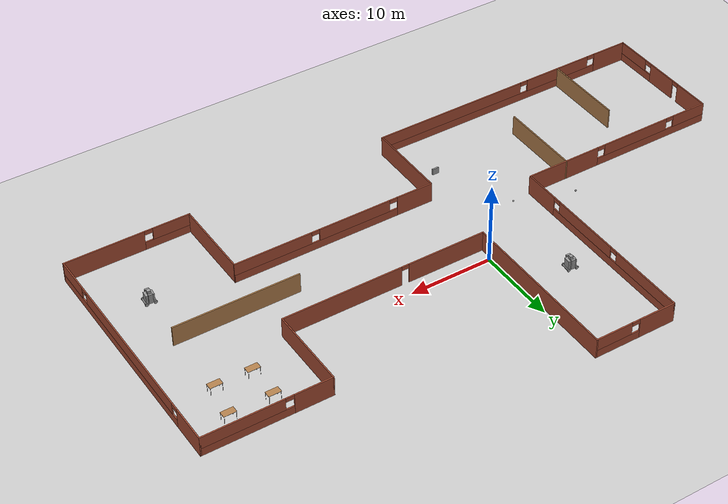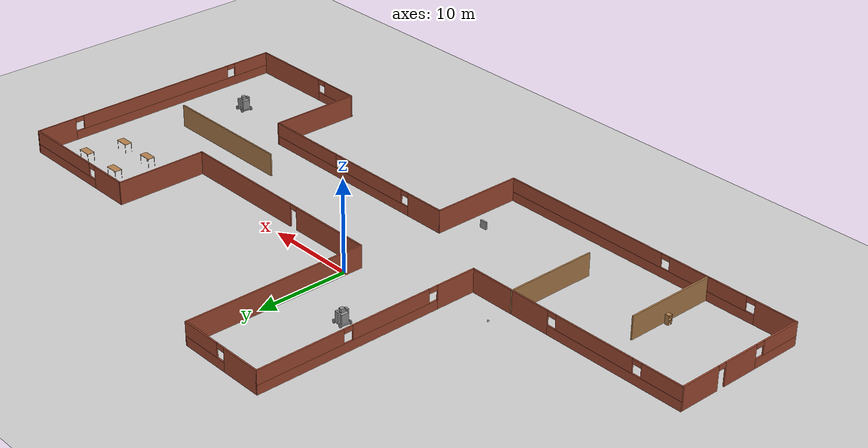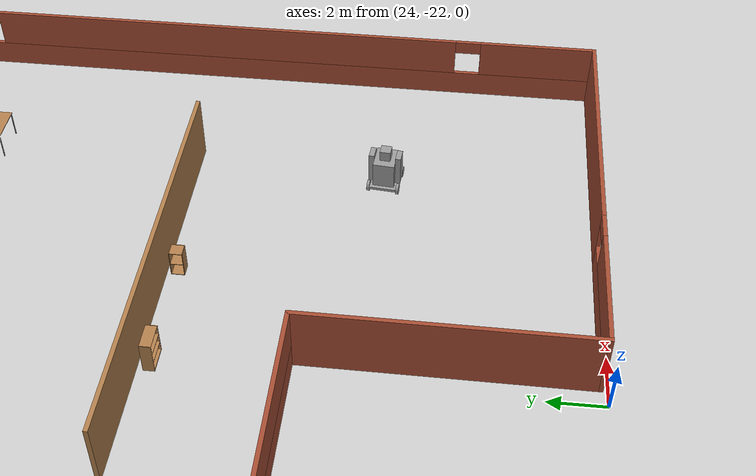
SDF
<sdf version="1.6">
 <world name="default">
  <plugin name="welcome_message" filename="libwelcome_message.so"/>
  <light name="sun" type="directional">
   <pose>0 0 10 0 -0 0</pose>
   <diffuse>0.8 0.8 0.8 1</diffuse>
   <specular>0.2 0.2 0.2 1</specular>
   <attenuation>
    <range>1000</range>
    <constant>0.9</constant>
    <linear>0.01</linear>
    <quadratic>0.001</quadratic>
   </attenuation>
   <direction>-0.5 0.1 -0.9</direction>
  </light>
  <model name="ground_plane">
   <static>1</static>
   <link name="link">
    <collision name="collision">
     <geometry><plane><normal>0 0 1</normal><size>100 100</size></plane></geometry>
     <surface>
      <contact><collide_bitmask>65535</collide_bitmask></contact>
      <friction><ode><mu>100</mu><mu2>50</mu2></ode></friction>
     </surface>
    </collision>
    <visual name="visual">
     <cast_shadows>0</cast_shadows>
     <geometry><plane><normal>0 0 1</normal><size>100 100</size></plane></geometry>
     <material>
      <script><uri>file://media/materials/scripts/gazebo.material</uri><name>Gazebo/Grey</name></script>
     </material>
    </visual>
   </link>
  </model>
  <gravity>0 0 -9.8</gravity>
  <magnetic_field>6e-06 2.3e-05 -4.2e-05</magnetic_field>
  <atmosphere type="adiabatic"/>
  <physics name="default_physics" default="0" type="ode">
   <max_step_size>0.001</max_step_size>
   <real_time_factor>1</real_time_factor>
   <real_time_update_rate>1000</real_time_update_rate>
  </physics>
  <scene><ambient>0.4 0.4 0.4 1</ambient><background>0.7 0.7 0.7 1</background><shadows>1</shadows></scene>
  <spherical_coordinates>
   <surface_model>EARTH_WGS84</surface_model>
   <latitude_deg>0</latitude_deg>
   <longitude_deg>0</longitude_deg>
   <elevation>0</elevation>
   <heading_deg>0</heading_deg>
  </spherical_coordinates>
  <model name="Building">
   <pose>2.1549 -1.76376 0 0 -0 0</pose>
   <link name="Wall_0">
    <pose>-12.5 7.5 0 0 -0 1.5708</pose>
    <visual name="Wall_0_Visual_0">
     <pose>-10.2875 0 1.25 0 -0 0</pose>
     <geometry><box><size>4.575 0.15 2.5</size></box></geometry>
     <material>
      <script><uri>file://media/materials/scripts/gazebo.material</uri><name>Gazebo/Bricks</name></script>
      <ambient>1 1 1 1</ambient>
     </material>
     <meta><layer>0</layer></meta>
    </visual>
    <collision name="Wall_0_Collision_0">
     <geometry><box><size>4.575 0.15 2.5</size></box></geometry>
     <pose>-10.2875 0 1.25 0 -0 0</pose>
    </collision>
    <visual name="Wall_0_Visual_1">
     <pose>2.2875 0 0.5 0 -0 0</pose>
     <geometry><box><size>20.575 0.15 1</size></box></geometry>
     <material>
      <script><uri>file://media/materials/scripts/gazebo.material</uri><name>Gazebo/Bricks</name></script>
      <ambient>1 1 1 1</ambient>
     </material>
     <meta><layer>0</layer></meta>
    </visual>
    <collision name="Wall_0_Collision_1">
     <geometry><box><size>20.575 0.15 1</size></box></geometry>
     <pose>2.2875 0 0.5 0 -0 0</pose>
    </collision>
    <visual name="Wall_0_Visual_2">
     <pose>-2.5 0 1.75 0 -0 0</pose>
     <geometry><box><size>9 0.15 1.5</size></box></geometry>
     <material>
      <script><uri>file://media/materials/scripts/gazebo.material</uri><name>Gazebo/Bricks</name></script>
      <ambient>1 1 1 1</ambient>
     </material>
     <meta><layer>0</layer></meta>
    </visual>
    <collision name="Wall_0_Collision_2">
     <geometry><box><size>9 0.15 1.5</size></box></geometry>
     <pose>-2.5 0 1.75 0 -0 0</pose>
    </collision>
    <visual name="Wall_0_Visual_3">
     <pose>7.7875 0 1.75 0 -0 0</pose>
     <geometry><box><size>9.575 0.15 1.5</size></box></geometry>
     <material>
      <script><uri>file://media/materials/scripts/gazebo.material</uri><name>Gazebo/Bricks</name></script>
      <ambient>1 1 1 1</ambient>
     </material>
     <meta><layer>0</layer></meta>
    </visual>
    <collision name="Wall_0_Collision_3">
     <geometry><box><size>9.575 0.15 1.5</size></box></geometry>
     <pose>7.7875 0 1.75 0 -0 0</pose>
    </collision>
    <visual name="Wall_0_Visual_4">
     <pose>-7.5 0 2.25 0 -0 0</pose>
     <geometry><box><size>1 0.15 0.5</size></box></geometry>
     <material>
      <script><uri>file://media/materials/scripts/gazebo.material</uri><name>Gazebo/Bricks</name></script>
      <ambient>1 1 1 1</ambient>
     </material>
     <meta><layer>0</layer></meta>
    </visual>
    <collision name="Wall_0_Collision_4">
     <geometry><box><size>1 0.15 0.5</size></box></geometry>
     <pose>-7.5 0 2.25 0 -0 0</pose>
    </collision>
    <visual name="Wall_0_Visual_5">
     <pose>2.5 0 2.25 0 -0 0</pose>
     <geometry><box><size>1 0.15 0.5</size></box></geometry>
     <material>
      <script><uri>file://media/materials/scripts/gazebo.material</uri><name>Gazebo/Bricks</name></script>
      <ambient>1 1 1 1</ambient>
     </material>
     <meta><layer>0</layer></meta>
    </visual>
    <collision name="Wall_0_Collision_5">
     <geometry><box><size>1 0.15 0.5</size></box></geometry>
     <pose>2.5 0 2.25 0 -0 0</pose>
    </collision>
   </link>
   <link name="Wall_11">
    <pose>30 10 0 0 -0 0</pose>
    <visual name="Wall_11_Visual_0">
     <pose>-5.2875 0 1.25 0 -0 0</pose>
     <geometry><box><size>4.575 0.15 2.5</size></box></geometry>
     <material>
      <script><uri>file://media/materials/scripts/gazebo.material</uri><name>Gazebo/Bricks</name></script>
      <ambient>1 1 1 1</ambient>
     </material>
     <meta><layer>0</layer></meta>
    </visual>
    <collision name="Wall_11_Collision_0">
     <geometry><box><size>4.575 0.15 2.5</size></box></geometry>
     <pose>-5.2875 0 1.25 0 -0 0</pose>
    </collision>
    <visual name="Wall_11_Visual_1">
     <pose>2.2875 0 0.5 0 -0 0</pose>
     <geometry><box><size>10.575 0.15 1</size></box></geometry>
     <material>
      <script><uri>file://media/materials/scripts/gazebo.material</uri><name>Gazebo/Bricks</name></script>
      <ambient>1 1 1 1</ambient>
     </material>
     <meta><layer>0</layer></meta>
    </visual>
    <collision name="Wall_11_Collision_1">
     <geometry><box><size>10.575 0.15 1</size></box></geometry>
     <pose>2.2875 0 0.5 0 -0 0</pose>
    </collision>
    <visual name="Wall_11_Visual_2">
     <pose>2.7875 0 1.75 0 -0 0</pose>
     <geometry><box><size>9.575 0.15 1.5</size></box></geometry>
     <material>
      <script><uri>file://media/materials/scripts/gazebo.material</uri><name>Gazebo/Bricks</name></script>
      <ambient>1 1 1 1</ambient>
     </material>
     <meta><layer>0</layer></meta>
    </visual>
    <collision name="Wall_11_Collision_2">
     <geometry><box><size>9.575 0.15 1.5</size></box></geometry>
     <pose>2.7875 0 1.75 0 -0 0</pose>
    </collision>
    <visual name="Wall_11_Visual_3">
     <pose>-2.5 0 2.25 0 -0 0</pose>
     <geometry><box><size>1 0.15 0.5</size></box></geometry>
     <material>
      <script><uri>file://media/materials/scripts/gazebo.material</uri><name>Gazebo/Bricks</name></script>
      <ambient>1 1 1 1</ambient>
     </material>
     <meta><layer>0</layer></meta>
    </visual>
    <collision name="Wall_11_Collision_3">
     <geometry><box><size>1 0.15 0.5</size></box></geometry>
     <pose>-2.5 0 2.25 0 -0 0</pose>
    </collision>
   </link>
   <link name="Wall_13">
    <pose>37.5 -4.925 0 0 0 -1.5708</pose>
    <visual name="Wall_13_Visual_0">
     <pose>-12.7125 0 1.25 0 -0 0</pose>
     <geometry><box><size>4.575 0.15 2.5</size></box></geometry>
     <material>
      <script><uri>file://media/materials/scripts/gazebo.material</uri><name>Gazebo/Bricks</name></script>
      <ambient>1 1 1 1</ambient>
     </material>
     <meta><layer>0</layer></meta>
    </visual>
    <collision name="Wall_13_Collision_0">
     <geometry><box><size>4.575 0.15 2.5</size></box></geometry>
     <pose>-12.7125 0 1.25 0 -0 0</pose>
    </collision>
    <visual name="Wall_13_Visual_1">
     <pose>2.2875 0 0.5 0 -0 0</pose>
     <geometry><box><size>25.425 0.15 1</size></box></geometry>
     <material>
      <script><uri>file://media/materials/scripts/gazebo.material</uri><name>Gazebo/Bricks</name></script>
      <ambient>1 1 1 1</ambient>
     </material>
     <meta><layer>0</layer></meta>
    </visual>
    <collision name="Wall_13_Collision_1">
     <geometry><box><size>25.425 0.15 1</size></box></geometry>
     <pose>2.2875 0 0.5 0 -0 0</pose>
    </collision>
    <visual name="Wall_13_Visual_2">
     <pose>0.075 0 1.75 0 -0 0</pose>
     <geometry><box><size>19 0.15 1.5</size></box></geometry>
     <material>
      <script><uri>file://media/materials/scripts/gazebo.material</uri><name>Gazebo/Bricks</name></script>
      <ambient>1 1 1 1</ambient>
     </material>
     <meta><layer>0</layer></meta>
    </visual>
    <collision name="Wall_13_Collision_2">
     <geometry><box><size>19 0.15 1.5</size></box></geometry>
     <pose>0.075 0 1.75 0 -0 0</pose>
    </collision>
    <visual name="Wall_13_Visual_3">
     <pose>12.7875 0 1.75 0 -0 0</pose>
     <geometry><box><size>4.425 0.15 1.5</size></box></geometry>
     <material>
      <script><uri>file://media/materials/scripts/gazebo.material</uri><name>Gazebo/Bricks</name></script>
      <ambient>1 1 1 1</ambient>
     </material>
     <meta><layer>0</layer></meta>
    </visual>
    <collision name="Wall_13_Collision_3">
     <geometry><box><size>4.425 0.15 1.5</size></box></geometry>
     <pose>12.7875 0 1.75 0 -0 0</pose>
    </collision>
    <visual name="Wall_13_Visual_4">
     <pose>-9.925 0 2.25 0 -0 0</pose>
     <geometry><box><size>1 0.15 0.5</size></box></geometry>
     <material>
      <script><uri>file://media/materials/scripts/gazebo.material</uri><name>Gazebo/Bricks</name></script>
      <ambient>1 1 1 1</ambient>
     </material>
     <meta><layer>0</layer></meta>
    </visual>
    <collision name="Wall_13_Collision_4">
     <geometry><box><size>1 0.15 0.5</size></box></geometry>
     <pose>-9.925 0 2.25 0 -0 0</pose>
    </collision>
    <visual name="Wall_13_Visual_5">
     <pose>10.075 0 2.25 0 -0 0</pose>
     <geometry><box><size>1 0.15 0.5</size></box></geometry>
     <material>
      <script><uri>file://media/materials/scripts/gazebo.material</uri><name>Gazebo/Bricks</name></script>
      <ambient>1 1 1 1</ambient>
     </material>
     <meta><layer>0</layer></meta>
    </visual>
    <collision name="Wall_13_Collision_5">
     <geometry><box><size>1 0.15 0.5</size></box></geometry>
     <pose>10.075 0 2.25 0 -0 0</pose>
    </collision>
   </link>
   <link name="Wall_15">
    <pose>30 -20 0 0 -0 3.14159</pose>
    <visual name="Wall_15_Visual_0">
     <pose>-2.7875 0 1.25 0 -0 0</pose>
     <geometry><box><size>9.575 0.15 2.5</size></box></geometry>
     <material>
      <script><uri>file://media/materials/scripts/gazebo.material</uri><name>Gazebo/Bricks</name></script>
      <ambient>1 1 1 1</ambient>
     </material>
     <meta><layer>0</layer></meta>
    </visual>
    <collision name="Wall_15_Collision_0">
     <geometry><box><size>9.575 0.15 2.5</size></box></geometry>
     <pose>-2.7875 0 1.25 0 -0 0</pose>
    </collision>
    <visual name="Wall_15_Visual_1">
     <pose>4.7875 0 0.5 0 -0 0</pose>
     <geometry><box><size>5.575 0.15 1</size></box></geometry>
     <material>
      <script><uri>file://media/materials/scripts/gazebo.material</uri><name>Gazebo/Bricks</name></script>
      <ambient>1 1 1 1</ambient>
     </material>
     <meta><layer>0</layer></meta>
    </visual>
    <collision name="Wall_15_Collision_1">
     <geometry><box><size>5.575 0.15 1</size></box></geometry>
     <pose>4.7875 0 0.5 0 -0 0</pose>
    </collision>
    <visual name="Wall_15_Visual_2">
     <pose>5.2875 0 1.75 0 -0 0</pose>
     <geometry><box><size>4.575 0.15 1.5</size></box></geometry>
     <material>
      <script><uri>file://media/materials/scripts/gazebo.material</uri><name>Gazebo/Bricks</name></script>
      <ambient>1 1 1 1</ambient>
     </material>
     <meta><layer>0</layer></meta>
    </visual>
    <collision name="Wall_15_Collision_2">
     <geometry><box><size>4.575 0.15 1.5</size></box></geometry>
     <pose>5.2875 0 1.75 0 -0 0</pose>
    </collision>
    <visual name="Wall_15_Visual_3">
     <pose>2.5 0 2.25 0 -0 0</pose>
     <geometry><box><size>1 0.15 0.5</size></box></geometry>
     <material>
      <script><uri>file://media/materials/scripts/gazebo.material</uri><name>Gazebo/Bricks</name></script>
      <ambient>1 1 1 1</ambient>
     </material>
     <meta><layer>0</layer></meta>
    </visual>
    <collision name="Wall_15_Collision_3">
     <geometry><box><size>1 0.15 0.5</size></box></geometry>
     <pose>2.5 0 2.25 0 -0 0</pose>
    </collision>
   </link>
   <link name="Wall_17">
    <collision name="Wall_17_Collision">
     <geometry><box><size>10.15 0.15 2.5</size></box></geometry>
     <pose>0 0 1.25 0 -0 0</pose>
    </collision>
    <visual name="Wall_17_Visual">
     <pose>0 0 1.25 0 -0 0</pose>
     <geometry><box><size>10.15 0.15 2.5</size></box></geometry>
     <material>
      <script><uri>file://media/materials/scripts/gazebo.material</uri><name>Gazebo/Bricks</name></script>
      <ambient>1 1 1 1</ambient>
     </material>
     <meta><layer>0</layer></meta>
    </visual>
    <pose>22.5 -15 0 0 -0 1.5708</pose>
   </link>
   <link name="Wall_19">
    <pose>-25 -5 0 0 -0 3.14159</pose>
    <visual name="Wall_19_Visual_0">
     <pose>-7.7875 0 1.25 0 -0 0</pose>
     <geometry><box><size>9.575 0.15 2.5</size></box></geometry>
     <material>
      <script><uri>file://media/materials/scripts/gazebo.material</uri><name>Gazebo/Bricks</name></script>
      <ambient>1 1 1 1</ambient>
     </material>
     <meta><layer>0</layer></meta>
    </visual>
    <collision name="Wall_19_Collision_0">
     <geometry><box><size>9.575 0.15 2.5</size></box></geometry>
     <pose>-7.7875 0 1.25 0 -0 0</pose>
    </collision>
    <visual name="Wall_19_Visual_1">
     <pose>4.7875 0 0.5 0 -0 0</pose>
     <geometry><box><size>15.575 0.15 1</size></box></geometry>
     <material>
      <script><uri>file://media/materials/scripts/gazebo.material</uri><name>Gazebo/Bricks</name></script>
      <ambient>1 1 1 1</ambient>
     </material>
     <meta><layer>0</layer></meta>
    </visual>
    <collision name="Wall_19_Collision_1">
     <geometry><box><size>15.575 0.15 1</size></box></geometry>
     <pose>4.7875 0 0.5 0 -0 0</pose>
    </collision>
    <visual name="Wall_19_Visual_2">
     <pose>2.5 0 1.75 0 -0 0</pose>
     <geometry><box><size>9 0.15 1.5</size></box></geometry>
     <material>
      <script><uri>file://media/materials/scripts/gazebo.material</uri><name>Gazebo/Bricks</name></script>
      <ambient>1 1 1 1</ambient>
     </material>
     <meta><layer>0</layer></meta>
    </visual>
    <collision name="Wall_19_Collision_2">
     <geometry><box><size>9 0.15 1.5</size></box></geometry>
     <pose>2.5 0 1.75 0 -0 0</pose>
    </collision>
    <visual name="Wall_19_Visual_3">
     <pose>10.2875 0 1.75 0 -0 0</pose>
     <geometry><box><size>4.575 0.15 1.5</size></box></geometry>
     <material>
      <script><uri>file://media/materials/scripts/gazebo.material</uri><name>Gazebo/Bricks</name></script>
      <ambient>1 1 1 1</ambient>
     </material>
     <meta><layer>0</layer></meta>
    </visual>
    <collision name="Wall_19_Collision_3">
     <geometry><box><size>4.575 0.15 1.5</size></box></geometry>
     <pose>10.2875 0 1.75 0 -0 0</pose>
    </collision>
    <visual name="Wall_19_Visual_4">
     <pose>-2.5 0 2.25 0 -0 0</pose>
     <geometry><box><size>1 0.15 0.5</size></box></geometry>
     <material>
      <script><uri>file://media/materials/scripts/gazebo.material</uri><name>Gazebo/Bricks</name></script>
      <ambient>1 1 1 1</ambient>
     </material>
     <meta><layer>0</layer></meta>
    </visual>
    <collision name="Wall_19_Collision_4">
     <geometry><box><size>1 0.15 0.5</size></box></geometry>
     <pose>-2.5 0 2.25 0 -0 0</pose>
    </collision>
    <visual name="Wall_19_Visual_5">
     <pose>7.5 0 2.25 0 -0 0</pose>
     <geometry><box><size>1 0.15 0.5</size></box></geometry>
     <material>
      <script><uri>file://media/materials/scripts/gazebo.material</uri><name>Gazebo/Bricks</name></script>
      <ambient>1 1 1 1</ambient>
     </material>
     <meta><layer>0</layer></meta>
    </visual>
    <collision name="Wall_19_Collision_5">
     <geometry><box><size>1 0.15 0.5</size></box></geometry>
     <pose>7.5 0 2.25 0 -0 0</pose>
    </collision>
   </link>
   <link name="Wall_2">
    <pose>-7.5 20 0 0 -0 0</pose>
    <visual name="Wall_2_Visual_0">
     <pose>-2.7875 0 1.25 0 -0 0</pose>
     <geometry><box><size>4.575 0.15 2.5</size></box></geometry>
     <material>
      <script><uri>file://media/materials/scripts/gazebo.material</uri><name>Gazebo/Bricks</name></script>
      <ambient>1 1 1 1</ambient>
     </material>
     <meta><layer>0</layer></meta>
    </visual>
    <collision name="Wall_2_Collision_0">
     <geometry><box><size>4.575 0.15 2.5</size></box></geometry>
     <pose>-2.7875 0 1.25 0 -0 0</pose>
    </collision>
    <visual name="Wall_2_Visual_1">
     <pose>2.2875 0 0.5 0 -0 0</pose>
     <geometry><box><size>5.575 0.15 1</size></box></geometry>
     <material>
      <script><uri>file://media/materials/scripts/gazebo.material</uri><name>Gazebo/Bricks</name></script>
      <ambient>1 1 1 1</ambient>
     </material>
     <meta><layer>0</layer></meta>
    </visual>
    <collision name="Wall_2_Collision_1">
     <geometry><box><size>5.575 0.15 1</size></box></geometry>
     <pose>2.2875 0 0.5 0 -0 0</pose>
    </collision>
    <visual name="Wall_2_Visual_2">
     <pose>2.7875 0 1.75 0 -0 0</pose>
     <geometry><box><size>4.575 0.15 1.5</size></box></geometry>
     <material>
      <script><uri>file://media/materials/scripts/gazebo.material</uri><name>Gazebo/Bricks</name></script>
      <ambient>1 1 1 1</ambient>
     </material>
     <meta><layer>0</layer></meta>
    </visual>
    <collision name="Wall_2_Collision_2">
     <geometry><box><size>4.575 0.15 1.5</size></box></geometry>
     <pose>2.7875 0 1.75 0 -0 0</pose>
    </collision>
    <visual name="Wall_2_Visual_3">
     <pose>0 0 2.25 0 -0 0</pose>
     <geometry><box><size>1 0.15 0.5</size></box></geometry>
     <material>
      <script><uri>file://media/materials/scripts/gazebo.material</uri><name>Gazebo/Bricks</name></script>
      <ambient>1 1 1 1</ambient>
     </material>
     <meta><layer>0</layer></meta>
    </visual>
    <collision name="Wall_2_Collision_3">
     <geometry><box><size>1 0.15 0.5</size></box></geometry>
     <pose>0 0 2.25 0 -0 0</pose>
    </collision>
   </link>
   <link name="Wall_21">
    <pose>-37.5 -12.5 0 0 0 -1.5708</pose>
    <visual name="Wall_21_Visual_0">
     <pose>-5.2625 0 1.25 0 -0 0</pose>
     <geometry><box><size>4.625 0.15 2.5</size></box></geometry>
     <material>
      <script><uri>file://media/materials/scripts/gazebo.material</uri><name>Gazebo/Bricks</name></script>
      <ambient>1 1 1 1</ambient>
     </material>
     <meta><layer>0</layer></meta>
    </visual>
    <collision name="Wall_21_Collision_0">
     <geometry><box><size>4.625 0.15 2.5</size></box></geometry>
     <pose>-5.2625 0 1.25 0 -0 0</pose>
    </collision>
    <visual name="Wall_21_Visual_1">
     <pose>-0.025 0 1.25 0 -0 0</pose>
     <geometry><box><size>4.05 0.15 2.5</size></box></geometry>
     <material>
      <script><uri>file://media/materials/scripts/gazebo.material</uri><name>Gazebo/Bricks</name></script>
      <ambient>1 1 1 1</ambient>
     </material>
     <meta><layer>0</layer></meta>
    </visual>
    <collision name="Wall_21_Collision_1">
     <geometry><box><size>4.05 0.15 2.5</size></box></geometry>
     <pose>-0.025 0 1.25 0 -0 0</pose>
    </collision>
    <visual name="Wall_21_Visual_2">
     <pose>4.7875 0 0.5 0 -0 0</pose>
     <geometry><box><size>5.575 0.15 1</size></box></geometry>
     <material>
      <script><uri>file://media/materials/scripts/gazebo.material</uri><name>Gazebo/Bricks</name></script>
      <ambient>1 1 1 1</ambient>
     </material>
     <meta><layer>0</layer></meta>
    </visual>
    <collision name="Wall_21_Collision_2">
     <geometry><box><size>5.575 0.15 1</size></box></geometry>
     <pose>4.7875 0 0.5 0 -0 0</pose>
    </collision>
    <visual name="Wall_21_Visual_3">
     <pose>5.2875 0 1.75 0 -0 0</pose>
     <geometry><box><size>4.575 0.15 1.5</size></box></geometry>
     <material>
      <script><uri>file://media/materials/scripts/gazebo.material</uri><name>Gazebo/Bricks</name></script>
      <ambient>1 1 1 1</ambient>
     </material>
     <meta><layer>0</layer></meta>
    </visual>
    <collision name="Wall_21_Collision_3">
     <geometry><box><size>4.575 0.15 1.5</size></box></geometry>
     <pose>5.2875 0 1.75 0 -0 0</pose>
    </collision>
    <visual name="Wall_21_Visual_4">
     <pose>-2.5 0 2.25 0 -0 0</pose>
     <geometry><box><size>0.9 0.15 0.5</size></box></geometry>
     <material>
      <script><uri>file://media/materials/scripts/gazebo.material</uri><name>Gazebo/Bricks</name></script>
      <ambient>1 1 1 1</ambient>
     </material>
     <meta><layer>0</layer></meta>
    </visual>
    <collision name="Wall_21_Collision_4">
     <geometry><box><size>0.9 0.15 0.5</size></box></geometry>
     <pose>-2.5 0 2.25 0 -0 0</pose>
    </collision>
    <visual name="Wall_21_Visual_5">
     <pose>2.5 0 2.25 0 -0 0</pose>
     <geometry><box><size>1 0.15 0.5</size></box></geometry>
     <material>
      <script><uri>file://media/materials/scripts/gazebo.material</uri><name>Gazebo/Bricks</name></script>
      <ambient>1 1 1 1</ambient>
     </material>
     <meta><layer>0</layer></meta>
    </visual>
    <collision name="Wall_21_Collision_5">
     <geometry><box><size>1 0.15 0.5</size></box></geometry>
     <pose>2.5 0 2.25 0 -0 0</pose>
    </collision>
   </link>
   <link name="Wall_23">
    <pose>-20 -20 0 0 -0 0</pose>
    <visual name="Wall_23_Visual_0">
     <pose>-15.2875 0 1.25 0 -0 0</pose>
     <geometry><box><size>4.575 0.15 2.5</size></box></geometry>
     <material>
      <script><uri>file://media/materials/scripts/gazebo.material</uri><name>Gazebo/Bricks</name></script>
      <ambient>1 1 1 1</ambient>
     </material>
     <meta><layer>0</layer></meta>
    </visual>
    <collision name="Wall_23_Collision_0">
     <geometry><box><size>4.575 0.15 2.5</size></box></geometry>
     <pose>-15.2875 0 1.25 0 -0 0</pose>
    </collision>
    <visual name="Wall_23_Visual_1">
     <pose>2.2875 0 0.5 0 -0 0</pose>
     <geometry><box><size>30.575 0.15 1</size></box></geometry>
     <material>
      <script><uri>file://media/materials/scripts/gazebo.material</uri><name>Gazebo/Bricks</name></script>
      <ambient>1 1 1 1</ambient>
     </material>
     <meta><layer>0</layer></meta>
    </visual>
    <collision name="Wall_23_Collision_1">
     <geometry><box><size>30.575 0.15 1</size></box></geometry>
     <pose>2.2875 0 0.5 0 -0 0</pose>
    </collision>
    <visual name="Wall_23_Visual_2">
     <pose>-7.5 0 1.75 0 -0 0</pose>
     <geometry><box><size>9 0.15 1.5</size></box></geometry>
     <material>
      <script><uri>file://media/materials/scripts/gazebo.material</uri><name>Gazebo/Bricks</name></script>
      <ambient>1 1 1 1</ambient>
     </material>
     <meta><layer>0</layer></meta>
    </visual>
    <collision name="Wall_23_Collision_2">
     <geometry><box><size>9 0.15 1.5</size></box></geometry>
     <pose>-7.5 0 1.75 0 -0 0</pose>
    </collision>
    <visual name="Wall_23_Visual_3">
     <pose>7.7875 0 1.75 0 -0 0</pose>
     <geometry><box><size>19.575 0.15 1.5</size></box></geometry>
     <material>
      <script><uri>file://media/materials/scripts/gazebo.material</uri><name>Gazebo/Bricks</name></script>
      <ambient>1 1 1 1</ambient>
     </material>
     <meta><layer>0</layer></meta>
    </visual>
    <collision name="Wall_23_Collision_3">
     <geometry><box><size>19.575 0.15 1.5</size></box></geometry>
     <pose>7.7875 0 1.75 0 -0 0</pose>
    </collision>
    <visual name="Wall_23_Visual_4">
     <pose>-12.5 0 2.25 0 -0 0</pose>
     <geometry><box><size>1 0.15 0.5</size></box></geometry>
     <material>
      <script><uri>file://media/materials/scripts/gazebo.material</uri><name>Gazebo/Bricks</name></script>
      <ambient>1 1 1 1</ambient>
     </material>
     <meta><layer>0</layer></meta>
    </visual>
    <collision name="Wall_23_Collision_4">
     <geometry><box><size>1 0.15 0.5</size></box></geometry>
     <pose>-12.5 0 2.25 0 -0 0</pose>
    </collision>
    <visual name="Wall_23_Visual_5">
     <pose>-2.5 0 2.25 0 -0 0</pose>
     <geometry><box><size>1 0.15 0.5</size></box></geometry>
     <material>
      <script><uri>file://media/materials/scripts/gazebo.material</uri><name>Gazebo/Bricks</name></script>
      <ambient>1 1 1 1</ambient>
     </material>
     <meta><layer>0</layer></meta>
    </visual>
    <collision name="Wall_23_Collision_5">
     <geometry><box><size>1 0.15 0.5</size></box></geometry>
     <pose>-2.5 0 2.25 0 -0 0</pose>
    </collision>
   </link>
   <link name="Wall_24">
    <collision name="Wall_24_Collision">
     <geometry><box><size>10.15 0.15 2.5</size></box></geometry>
     <pose>0 0 1.25 0 -0 0</pose>
    </collision>
    <visual name="Wall_24_Visual">
     <pose>0 0 1.25 0 -0 0</pose>
     <geometry><box><size>10.15 0.15 2.5</size></box></geometry>
     <material>
      <script><uri>file://media/materials/scripts/gazebo.material</uri><name>Gazebo/Bricks</name></script>
      <ambient>1 1 1 1</ambient>
     </material>
     <meta><layer>0</layer></meta>
    </visual>
    <pose>-2.5 -15 0 0 -0 1.5708</pose>
   </link>
   <link name="Wall_26">
    <pose>10 -10 0 0 -0 0</pose>
    <visual name="Wall_26_Visual_0">
     <pose>-10.2875 0 1.25 0 -0 0</pose>
     <geometry><box><size>4.575 0.15 2.5</size></box></geometry>
     <material>
      <script><uri>file://media/materials/scripts/gazebo.material</uri><name>Gazebo/Bricks</name></script>
      <ambient>1 1 1 1</ambient>
     </material>
     <meta><layer>0</layer></meta>
    </visual>
    <collision name="Wall_26_Collision_0">
     <geometry><box><size>4.575 0.15 2.5</size></box></geometry>
     <pose>-10.2875 0 1.25 0 -0 0</pose>
    </collision>
    <visual name="Wall_26_Visual_1">
     <pose>2.2875 0 0.5 0 -0 0</pose>
     <geometry><box><size>20.575 0.15 1</size></box></geometry>
     <material>
      <script><uri>file://media/materials/scripts/gazebo.material</uri><name>Gazebo/Bricks</name></script>
      <ambient>1 1 1 1</ambient>
     </material>
     <meta><layer>0</layer></meta>
    </visual>
    <collision name="Wall_26_Collision_1">
     <geometry><box><size>20.575 0.15 1</size></box></geometry>
     <pose>2.2875 0 0.5 0 -0 0</pose>
    </collision>
    <visual name="Wall_26_Visual_2">
     <pose>-2.5 0 1.75 0 -0 0</pose>
     <geometry><box><size>9 0.15 1.5</size></box></geometry>
     <material>
      <script><uri>file://media/materials/scripts/gazebo.material</uri><name>Gazebo/Bricks</name></script>
      <ambient>1 1 1 1</ambient>
     </material>
     <meta><layer>0</layer></meta>
    </visual>
    <collision name="Wall_26_Collision_2">
     <geometry><box><size>9 0.15 1.5</size></box></geometry>
     <pose>-2.5 0 1.75 0 -0 0</pose>
    </collision>
    <visual name="Wall_26_Visual_3">
     <pose>7.7875 0 1.75 0 -0 0</pose>
     <geometry><box><size>9.575 0.15 1.5</size></box></geometry>
     <material>
      <script><uri>file://media/materials/scripts/gazebo.material</uri><name>Gazebo/Bricks</name></script>
      <ambient>1 1 1 1</ambient>
     </material>
     <meta><layer>0</layer></meta>
    </visual>
    <collision name="Wall_26_Collision_3">
     <geometry><box><size>9.575 0.15 1.5</size></box></geometry>
     <pose>7.7875 0 1.75 0 -0 0</pose>
    </collision>
    <visual name="Wall_26_Visual_4">
     <pose>-7.5 0 2.25 0 -0 0</pose>
     <geometry><box><size>1 0.15 0.5</size></box></geometry>
     <material>
      <script><uri>file://media/materials/scripts/gazebo.material</uri><name>Gazebo/Bricks</name></script>
      <ambient>1 1 1 1</ambient>
     </material>
     <meta><layer>0</layer></meta>
    </visual>
    <collision name="Wall_26_Collision_4">
     <geometry><box><size>1 0.15 0.5</size></box></geometry>
     <pose>-7.5 0 2.25 0 -0 0</pose>
    </collision>
    <visual name="Wall_26_Visual_5">
     <pose>2.5 0 2.25 0 -0 0</pose>
     <geometry><box><size>1 0.15 0.5</size></box></geometry>
     <material>
      <script><uri>file://media/materials/scripts/gazebo.material</uri><name>Gazebo/Bricks</name></script>
      <ambient>1 1 1 1</ambient>
     </material>
     <meta><layer>0</layer></meta>
    </visual>
    <collision name="Wall_26_Collision_5">
     <geometry><box><size>1 0.15 0.5</size></box></geometry>
     <pose>2.5 0 2.25 0 -0 0</pose>
    </collision>
   </link>
   <link name="Wall_28">
    <collision name="Wall_28_Collision">
     <geometry><box><size>15.15 0.15 2.5</size></box></geometry>
     <pose>0 0 1.25 0 -0 0</pose>
    </collision>
    <visual name="Wall_28_Visual">
     <pose>0 0 1.25 0 -0 0</pose>
     <geometry><box><size>15.15 0.15 2.5</size></box></geometry>
     <material>
      <script><uri>file://media/materials/scripts/gazebo.material</uri><name>Gazebo/Wood</name></script>
      <ambient>1 1 1 1</ambient>
     </material>
     <meta><layer>0</layer></meta>
    </visual>
    <pose>25 -5 0 0 -0 0</pose>
   </link>
   <link name="Wall_30">
    <collision name="Wall_30_Collision">
     <geometry><box><size>10.15 0.15 2.5</size></box></geometry>
     <pose>0 0 1.25 0 -0 0</pose>
    </collision>
    <visual name="Wall_30_Visual">
     <pose>0 0 1.25 0 -0 0</pose>
     <geometry><box><size>10.15 0.15 2.5</size></box></geometry>
     <material>
      <script><uri>file://media/materials/scripts/gazebo.material</uri><name>Gazebo/Wood</name></script>
      <ambient>1 1 1 1</ambient>
     </material>
     <meta><layer>0</layer></meta>
    </visual>
    <pose>-27.5 -15 0 0 0 -1.5708</pose>
   </link>
   <link name="Wall_32">
    <collision name="Wall_32_Collision">
     <geometry><box><size>10.15 0.15 2.5</size></box></geometry>
     <pose>0 0 1.25 0 -0 0</pose>
    </collision>
    <visual name="Wall_32_Visual">
     <pose>0 0 1.25 0 -0 0</pose>
     <geometry><box><size>10.15 0.15 2.5</size></box></geometry>
     <material>
      <script><uri>file://media/materials/scripts/gazebo.material</uri><name>Gazebo/Wood</name></script>
      <ambient>1 1 1 1</ambient>
     </material>
     <meta><layer>0</layer></meta>
    </visual>
    <pose>-17.5 -10 0 0 0 -1.5708</pose>
   </link>
   <link name="Wall_4">
    <collision name="Wall_4_Collision">
     <geometry><box><size>20.15 0.15 2.5</size></box></geometry>
     <pose>0 0 1.25 0 -0 0</pose>
    </collision>
    <visual name="Wall_4_Visual">
     <pose>0 0 1.25 0 -0 0</pose>
     <geometry><box><size>20.15 0.15 2.5</size></box></geometry>
     <material>
      <script><uri>file://media/materials/scripts/gazebo.material</uri><name>Gazebo/Bricks</name></script>
      <ambient>1 1 1 1</ambient>
     </material>
     <meta><layer>0</layer></meta>
    </visual>
    <pose>-2.5 10 0 0 0 -1.5708</pose>
   </link>
   <link name="Wall_6">
    <pose>10 0 0 0 -0 0</pose>
    <visual name="Wall_6_Visual_0">
     <pose>-7.7625 0 1.25 0 -0 0</pose>
     <geometry><box><size>9.625 0.15 2.5</size></box></geometry>
     <material>
      <script><uri>file://media/materials/scripts/gazebo.material</uri><name>Gazebo/Bricks</name></script>
      <ambient>1 1 1 1</ambient>
     </material>
     <meta><layer>0</layer></meta>
    </visual>
    <collision name="Wall_6_Collision_0">
     <geometry><box><size>9.625 0.15 2.5</size></box></geometry>
     <pose>-7.7625 0 1.25 0 -0 0</pose>
    </collision>
    <visual name="Wall_6_Visual_1">
     <pose>5.2625 0 1.25 0 -0 0</pose>
     <geometry><box><size>14.625 0.15 2.5</size></box></geometry>
     <material>
      <script><uri>file://media/materials/scripts/gazebo.material</uri><name>Gazebo/Bricks</name></script>
      <ambient>1 1 1 1</ambient>
     </material>
     <meta><layer>0</layer></meta>
    </visual>
    <collision name="Wall_6_Collision_1">
     <geometry><box><size>14.625 0.15 2.5</size></box></geometry>
     <pose>5.2625 0 1.25 0 -0 0</pose>
    </collision>
    <visual name="Wall_6_Visual_2">
     <pose>-2.5 0 2.25 0 -0 0</pose>
     <geometry><box><size>0.9 0.15 0.5</size></box></geometry>
     <material>
      <script><uri>file://media/materials/scripts/gazebo.material</uri><name>Gazebo/Bricks</name></script>
      <ambient>1 1 1 1</ambient>
     </material>
     <meta><layer>0</layer></meta>
    </visual>
    <collision name="Wall_6_Collision_2">
     <geometry><box><size>0.9 0.15 0.5</size></box></geometry>
     <pose>-2.5 0 2.25 0 -0 0</pose>
    </collision>
   </link>
   <link name="Wall_9">
    <collision name="Wall_9_Collision">
     <geometry><box><size>10.15 0.15 2.5</size></box></geometry>
     <pose>0 0 1.25 0 -0 0</pose>
    </collision>
    <visual name="Wall_9_Visual">
     <pose>0 0 1.25 0 -0 0</pose>
     <geometry><box><size>10.15 0.15 2.5</size></box></geometry>
     <material>
      <script><uri>file://media/materials/scripts/gazebo.material</uri><name>Gazebo/Bricks</name></script>
      <ambient>1 1 1 1</ambient>
     </material>
     <meta><layer>0</layer></meta>
    </visual>
    <pose>22.5 5 0 0 -0 1.5708</pose>
   </link>
   <link name="Window_9">
    <collision name="Window_9_Collision">
     <geometry><box><size>0.8 0.17 0.8</size></box></geometry>
     <pose>0 0 0.4 0 -0 0</pose>
    </collision>
    <visual name="Window_9_Visual">
     <pose>0 0 0.4 0 -0 0</pose>
     <geometry><box><size>0.8 0.17 0.8</size></box></geometry>
     <material>
      <script><uri>file://media/materials/scripts/gazebo.material</uri><name>Gazebo/Grey</name></script>
     </material>
    </visual>
    <pose>-5.28751 -13.263 0.5 0 -0 0</pose>
   </link>
   <static>1</static>
  </model>
  <model name="HumanoidRobot">
   <link name="link_0">
    <pose>-0.322222 -0.151781 0.006429 -0 -0 -0</pose>
    <inertial>
     <mass>1</mass>
     <inertia>
      <ixx>0.166667</ixx>
      <ixy>0</ixy>
      <ixz>0</ixz>
      <iyy>0.166667</iyy>
      <iyz>0</iyz>
      <izz>0.166667</izz>
     </inertia>
    </inertial>
    <visual name="visual">
     <geometry><box><size>0.3 1 0.1</size></box></geometry>
     <material>
      <lighting>1</lighting>
      <script><uri>file://media/materials/scripts/gazebo.material</uri><name>Gazebo/Grey</name></script>
      <shader type="pixel"><normal_map>__default__</normal_map></shader>
      <ambient>0.3 0.3 0.3 1</ambient>
      <diffuse>0.7 0.7 0.7 1</diffuse>
      <specular>0.01 0.01 0.01 1</specular>
      <emissive>0 0 0 1</emissive>
     </material>
    </visual>
    <collision name="collision">
     <geometry><box><size>0.3 1 0.1</size></box></geometry>
     <surface>
      <friction>
       <ode><mu>1</mu><mu2>1</mu2><fdir1>0 0 0</fdir1><slip1>0</slip1><slip2>0</slip2></ode>
       <torsional>
        <coefficient>1</coefficient>
        <patch_radius>0</patch_radius>
        <surface_radius>0</surface_radius>
        <use_patch_radius>1</use_patch_radius>
        <ode><slip>0</slip></ode>
       </torsional>
      </friction>
      <bounce><restitution_coefficient>0</restitution_coefficient><threshold>1e+06</threshold></bounce>
      <contact>
       <collide_without_contact>0</collide_without_contact>
       <collide_without_contact_bitmask>1</collide_without_contact_bitmask>
       <collide_bitmask>1</collide_bitmask>
       <ode>
        <soft_cfm>0</soft_cfm>
        <soft_erp>0.2</soft_erp>
        <kp>1e+13</kp>
        <kd>1</kd>
        <max_vel>0.01</max_vel>
        <min_depth>0</min_depth>
       </ode>
       <bullet>
        <split_impulse>1</split_impulse>
        <split_impulse_penetration_threshold>-0.01</split_impulse_penetration_threshold>
        <soft_cfm>0</soft_cfm>
        <soft_erp>0.2</soft_erp>
        <kp>1e+13</kp>
        <kd>1</kd>
       </bullet>
      </contact>
     </surface>
    </collision>
   </link>
   <link name="link_0_clone">
    <pose>0.677778 -0.151781 0.006429 -0 -0 -0</pose>
    <inertial>
     <mass>1</mass>
     <inertia>
      <ixx>0.166667</ixx>
      <ixy>0</ixy>
      <ixz>0</ixz>
      <iyy>0.166667</iyy>
      <iyz>0</iyz>
      <izz>0.166667</izz>
     </inertia>
    </inertial>
    <visual name="visual">
     <geometry><box><size>0.3 1 0.1</size></box></geometry>
     <material>
      <lighting>1</lighting>
      <script><uri>file://media/materials/scripts/gazebo.material</uri><name>Gazebo/Grey</name></script>
      <shader type="pixel"><normal_map>__default__</normal_map></shader>
      <ambient>0.3 0.3 0.3 1</ambient>
      <diffuse>0.7 0.7 0.7 1</diffuse>
      <specular>0.01 0.01 0.01 1</specular>
      <emissive>0 0 0 1</emissive>
     </material>
    </visual>
    <collision name="collision">
     <geometry><box><size>0.3 1 0.1</size></box></geometry>
     <surface>
      <friction>
       <ode><mu>1</mu><mu2>1</mu2><fdir1>0 0 0</fdir1><slip1>0</slip1><slip2>0</slip2></ode>
       <torsional>
        <coefficient>1</coefficient>
        <patch_radius>0</patch_radius>
        <surface_radius>0</surface_radius>
        <use_patch_radius>1</use_patch_radius>
        <ode><slip>0</slip></ode>
       </torsional>
      </friction>
      <bounce><restitution_coefficient>0</restitution_coefficient><threshold>1e+06</threshold></bounce>
      <contact>
       <collide_without_contact>0</collide_without_contact>
       <collide_without_contact_bitmask>1</collide_without_contact_bitmask>
       <collide_bitmask>1</collide_bitmask>
       <ode>
        <soft_cfm>0</soft_cfm>
        <soft_erp>0.2</soft_erp>
        <kp>1e+13</kp>
        <kd>1</kd>
        <max_vel>0.01</max_vel>
        <min_depth>0</min_depth>
       </ode>
       <bullet>
        <split_impulse>1</split_impulse>
        <split_impulse_penetration_threshold>-0.01</split_impulse_penetration_threshold>
        <soft_cfm>0</soft_cfm>
        <soft_erp>0.2</soft_erp>
        <kp>1e+13</kp>
        <kd>1</kd>
       </bullet>
      </contact>
     </surface>
    </collision>
   </link>
   <link name="link_1">
    <pose>-0.322222 -0.7018 0.006429 1.5707 -0 0</pose>
    <inertial>
     <mass>1</mass>
     <inertia><ixx>0.145833</ixx><ixy>0</ixy><ixz>0</ixz><iyy>0.145833</iyy><iyz>0</iyz><izz>0.125</izz></inertia>
    </inertial>
    <visual name="visual">
     <geometry><cylinder><radius>0.2</radius><length>0.1</length></cylinder></geometry>
     <material>
      <lighting>1</lighting>
      <script><uri>file://media/materials/scripts/gazebo.material</uri><name>Gazebo/Grey</name></script>
      <shader type="pixel"><normal_map>__default__</normal_map></shader>
      <ambient>0.3 0.3 0.3 1</ambient>
      <diffuse>0.7 0.7 0.7 1</diffuse>
      <specular>0.01 0.01 0.01 1</specular>
      <emissive>0 0 0 1</emissive>
     </material>
    </visual>
    <collision name="collision">
     <geometry><cylinder><radius>0.2</radius><length>0.1</length></cylinder></geometry>
     <surface>
      <friction>
       <ode><mu>1</mu><mu2>1</mu2><fdir1>0 0 0</fdir1><slip1>0</slip1><slip2>0</slip2></ode>
       <torsional>
        <coefficient>1</coefficient>
        <patch_radius>0</patch_radius>
        <surface_radius>0</surface_radius>
        <use_patch_radius>1</use_patch_radius>
        <ode><slip>0</slip></ode>
       </torsional>
      </friction>
      <bounce><restitution_coefficient>0</restitution_coefficient><threshold>1e+06</threshold></bounce>
      <contact>
       <collide_without_contact>0</collide_without_contact>
       <collide_without_contact_bitmask>1</collide_without_contact_bitmask>
       <collide_bitmask>1</collide_bitmask>
       <ode>
        <soft_cfm>0</soft_cfm>
        <soft_erp>0.2</soft_erp>
        <kp>1e+13</kp>
        <kd>1</kd>
        <max_vel>0.01</max_vel>
        <min_depth>0</min_depth>
       </ode>
       <bullet>
        <split_impulse>1</split_impulse>
        <split_impulse_penetration_threshold>-0.01</split_impulse_penetration_threshold>
        <soft_cfm>0</soft_cfm>
        <soft_erp>0.2</soft_erp>
        <kp>1e+13</kp>
        <kd>1</kd>
       </bullet>
      </contact>
     </surface>
    </collision>
   </link>
   <link name="link_1_clone">
    <pose>-0.322222 0.398238 0.006429 1.5707 -0 0</pose>
    <inertial>
     <mass>1</mass>
     <inertia><ixx>0.145833</ixx><ixy>0</ixy><ixz>0</ixz><iyy>0.145833</iyy><iyz>0</iyz><izz>0.125</izz></inertia>
    </inertial>
    <visual name="visual">
     <geometry><cylinder><radius>0.2</radius><length>0.1</length></cylinder></geometry>
     <material>
      <lighting>1</lighting>
      <script><uri>file://media/materials/scripts/gazebo.material</uri><name>Gazebo/Grey</name></script>
      <shader type="pixel"><normal_map>__default__</normal_map></shader>
      <ambient>0.3 0.3 0.3 1</ambient>
      <diffuse>0.7 0.7 0.7 1</diffuse>
      <specular>0.01 0.01 0.01 1</specular>
      <emissive>0 0 0 1</emissive>
     </material>
    </visual>
    <collision name="collision">
     <geometry><cylinder><radius>0.2</radius><length>0.1</length></cylinder></geometry>
     <surface>
      <friction>
       <ode><mu>1</mu><mu2>1</mu2><fdir1>0 0 0</fdir1><slip1>0</slip1><slip2>0</slip2></ode>
       <torsional>
        <coefficient>1</coefficient>
        <patch_radius>0</patch_radius>
        <surface_radius>0</surface_radius>
        <use_patch_radius>1</use_patch_radius>
        <ode><slip>0</slip></ode>
       </torsional>
      </friction>
      <bounce><restitution_coefficient>0</restitution_coefficient><threshold>1e+06</threshold></bounce>
      <contact>
       <collide_without_contact>0</collide_without_contact>
       <collide_without_contact_bitmask>1</collide_without_contact_bitmask>
       <collide_bitmask>1</collide_bitmask>
       <ode>
        <soft_cfm>0</soft_cfm>
        <soft_erp>0.2</soft_erp>
        <kp>1e+13</kp>
        <kd>1</kd>
        <max_vel>0.01</max_vel>
        <min_depth>0</min_depth>
       </ode>
       <bullet>
        <split_impulse>1</split_impulse>
        <split_impulse_penetration_threshold>-0.01</split_impulse_penetration_threshold>
        <soft_cfm>0</soft_cfm>
        <soft_erp>0.2</soft_erp>
        <kp>1e+13</kp>
        <kd>1</kd>
       </bullet>
      </contact>
     </surface>
    </collision>
   </link>
   <link name="link_1_clone_0">
    <pose>0.677778 0.398238 0.006429 1.5707 -0 0</pose>
    <inertial>
     <mass>1</mass>
     <inertia><ixx>0.145833</ixx><ixy>0</ixy><ixz>0</ixz><iyy>0.145833</iyy><iyz>0</iyz><izz>0.125</izz></inertia>
    </inertial>
    <visual name="visual">
     <geometry><cylinder><radius>0.2</radius><length>0.1</length></cylinder></geometry>
     <material>
      <lighting>1</lighting>
      <script><uri>file://media/materials/scripts/gazebo.material</uri><name>Gazebo/Grey</name></script>
      <shader type="pixel"><normal_map>__default__</normal_map></shader>
      <ambient>0.3 0.3 0.3 1</ambient>
      <diffuse>0.7 0.7 0.7 1</diffuse>
      <specular>0.01 0.01 0.01 1</specular>
      <emissive>0 0 0 1</emissive>
     </material>
    </visual>
    <collision name="collision">
     <geometry><cylinder><radius>0.2</radius><length>0.1</length></cylinder></geometry>
     <surface>
      <friction>
       <ode><mu>1</mu><mu2>1</mu2><fdir1>0 0 0</fdir1><slip1>0</slip1><slip2>0</slip2></ode>
       <torsional>
        <coefficient>1</coefficient>
        <patch_radius>0</patch_radius>
        <surface_radius>0</surface_radius>
        <use_patch_radius>1</use_patch_radius>
        <ode><slip>0</slip></ode>
       </torsional>
      </friction>
      <bounce><restitution_coefficient>0</restitution_coefficient><threshold>1e+06</threshold></bounce>
      <contact>
       <collide_without_contact>0</collide_without_contact>
       <collide_without_contact_bitmask>1</collide_without_contact_bitmask>
       <collide_bitmask>1</collide_bitmask>
       <ode>
        <soft_cfm>0</soft_cfm>
        <soft_erp>0.2</soft_erp>
        <kp>1e+13</kp>
        <kd>1</kd>
        <max_vel>0.01</max_vel>
        <min_depth>0</min_depth>
       </ode>
       <bullet>
        <split_impulse>1</split_impulse>
        <split_impulse_penetration_threshold>-0.01</split_impulse_penetration_threshold>
        <soft_cfm>0</soft_cfm>
        <soft_erp>0.2</soft_erp>
        <kp>1e+13</kp>
        <kd>1</kd>
       </bullet>
      </contact>
     </surface>
    </collision>
   </link>
   <link name="link_1_clone_1">
    <pose>0.677778 -0.7018 0.006429 1.5707 -0 0</pose>
    <inertial>
     <mass>1</mass>
     <inertia><ixx>0.145833</ixx><ixy>0</ixy><ixz>0</ixz><iyy>0.145833</iyy><iyz>0</iyz><izz>0.125</izz></inertia>
    </inertial>
    <visual name="visual">
     <geometry><cylinder><radius>0.2</radius><length>0.1</length></cylinder></geometry>
     <material>
      <lighting>1</lighting>
      <script><uri>file://media/materials/scripts/gazebo.material</uri><name>Gazebo/Grey</name></script>
      <shader type="pixel"><normal_map>__default__</normal_map></shader>
      <ambient>0.3 0.3 0.3 1</ambient>
      <diffuse>0.7 0.7 0.7 1</diffuse>
      <specular>0.01 0.01 0.01 1</specular>
      <emissive>0 0 0 1</emissive>
     </material>
    </visual>
    <collision name="collision">
     <geometry><cylinder><radius>0.2</radius><length>0.1</length></cylinder></geometry>
     <surface>
      <friction>
       <ode><mu>1</mu><mu2>1</mu2><fdir1>0 0 0</fdir1><slip1>0</slip1><slip2>0</slip2></ode>
       <torsional>
        <coefficient>1</coefficient>
        <patch_radius>0</patch_radius>
        <surface_radius>0</surface_radius>
        <use_patch_radius>1</use_patch_radius>
        <ode><slip>0</slip></ode>
       </torsional>
      </friction>
      <bounce><restitution_coefficient>0</restitution_coefficient><threshold>1e+06</threshold></bounce>
      <contact>
       <collide_without_contact>0</collide_without_contact>
       <collide_without_contact_bitmask>1</collide_without_contact_bitmask>
       <collide_bitmask>1</collide_bitmask>
       <ode>
        <soft_cfm>0</soft_cfm>
        <soft_erp>0.2</soft_erp>
        <kp>1e+13</kp>
        <kd>1</kd>
        <max_vel>0.01</max_vel>
        <min_depth>0</min_depth>
       </ode>
       <bullet>
        <split_impulse>1</split_impulse>
        <split_impulse_penetration_threshold>-0.01</split_impulse_penetration_threshold>
        <soft_cfm>0</soft_cfm>
        <soft_erp>0.2</soft_erp>
        <kp>1e+13</kp>
        <kd>1</kd>
       </bullet>
      </contact>
     </surface>
    </collision>
   </link>
   <link name="link_2">
    <pose>0.177778 -0.151781 0.556429 -0 -0 -0</pose>
    <inertial>
     <mass>1</mass>
     <inertia>
      <ixx>0.166667</ixx>
      <ixy>0</ixy>
      <ixz>0</ixz>
      <iyy>0.166667</iyy>
      <iyz>0</iyz>
      <izz>0.166667</izz>
     </inertia>
    </inertial>
    <visual name="visual">
     <geometry><box><size>1 0.8 1</size></box></geometry>
     <material>
      <lighting>1</lighting>
      <script><uri>file://media/materials/scripts/gazebo.material</uri><name>Gazebo/Grey</name></script>
      <shader type="pixel"><normal_map>__default__</normal_map></shader>
      <ambient>0.3 0.3 0.3 1</ambient>
      <diffuse>0.7 0.7 0.7 1</diffuse>
      <specular>0.01 0.01 0.01 1</specular>
      <emissive>0 0 0 1</emissive>
     </material>
    </visual>
    <collision name="collision">
     <geometry><box><size>1 0.8 1</size></box></geometry>
     <surface>
      <friction>
       <ode><mu>1</mu><mu2>1</mu2><fdir1>0 0 0</fdir1><slip1>0</slip1><slip2>0</slip2></ode>
       <torsional>
        <coefficient>1</coefficient>
        <patch_radius>0</patch_radius>
        <surface_radius>0</surface_radius>
        <use_patch_radius>1</use_patch_radius>
        <ode><slip>0</slip></ode>
       </torsional>
      </friction>
      <bounce><restitution_coefficient>0</restitution_coefficient><threshold>1e+06</threshold></bounce>
      <contact>
       <collide_without_contact>0</collide_without_contact>
       <collide_without_contact_bitmask>1</collide_without_contact_bitmask>
       <collide_bitmask>1</collide_bitmask>
       <ode>
        <soft_cfm>0</soft_cfm>
        <soft_erp>0.2</soft_erp>
        <kp>1e+13</kp>
        <kd>1</kd>
        <max_vel>0.01</max_vel>
        <min_depth>0</min_depth>
       </ode>
       <bullet>
        <split_impulse>1</split_impulse>
        <split_impulse_penetration_threshold>-0.01</split_impulse_penetration_threshold>
        <soft_cfm>0</soft_cfm>
        <soft_erp>0.2</soft_erp>
        <kp>1e+13</kp>
        <kd>1</kd>
       </bullet>
      </contact>
     </surface>
    </collision>
   </link>
   <link name="link_3">
    <pose>0.177778 0.348219 0.656429 -0 -0 -0</pose>
    <inertial>
     <mass>1</mass>
     <inertia>
      <ixx>0.166667</ixx>
      <ixy>0</ixy>
      <ixz>0</ixz>
      <iyy>0.166667</iyy>
      <iyz>0</iyz>
      <izz>0.166667</izz>
     </inertia>
    </inertial>
    <visual name="visual">
     <geometry><box><size>0.5 0.2 1.2</size></box></geometry>
     <material>
      <lighting>1</lighting>
      <script><uri>file://media/materials/scripts/gazebo.material</uri><name>Gazebo/Grey</name></script>
      <shader type="pixel"><normal_map>__default__</normal_map></shader>
      <ambient>0.3 0.3 0.3 1</ambient>
      <diffuse>0.7 0.7 0.7 1</diffuse>
      <specular>0.01 0.01 0.01 1</specular>
      <emissive>0 0 0 1</emissive>
     </material>
    </visual>
    <collision name="collision">
     <geometry><box><size>0.5 0.2 1.2</size></box></geometry>
     <surface>
      <friction>
       <ode><mu>1</mu><mu2>1</mu2><fdir1>0 0 0</fdir1><slip1>0</slip1><slip2>0</slip2></ode>
       <torsional>
        <coefficient>1</coefficient>
        <patch_radius>0</patch_radius>
        <surface_radius>0</surface_radius>
        <use_patch_radius>1</use_patch_radius>
        <ode><slip>0</slip></ode>
       </torsional>
      </friction>
      <bounce><restitution_coefficient>0</restitution_coefficient><threshold>1e+06</threshold></bounce>
      <contact>
       <collide_without_contact>0</collide_without_contact>
       <collide_without_contact_bitmask>1</collide_without_contact_bitmask>
       <collide_bitmask>1</collide_bitmask>
       <ode>
        <soft_cfm>0</soft_cfm>
        <soft_erp>0.2</soft_erp>
        <kp>1e+13</kp>
        <kd>1</kd>
        <max_vel>0.01</max_vel>
        <min_depth>0</min_depth>
       </ode>
       <bullet>
        <split_impulse>1</split_impulse>
        <split_impulse_penetration_threshold>-0.01</split_impulse_penetration_threshold>
        <soft_cfm>0</soft_cfm>
        <soft_erp>0.2</soft_erp>
        <kp>1e+13</kp>
        <kd>1</kd>
       </bullet>
      </contact>
     </surface>
    </collision>
   </link>
   <link name="link_3_clone">
    <pose>0.177778 -0.651781 0.65643 -0 -0 -0</pose>
    <inertial>
     <mass>1</mass>
     <inertia>
      <ixx>0.166667</ixx>
      <ixy>0</ixy>
      <ixz>0</ixz>
      <iyy>0.166667</iyy>
      <iyz>0</iyz>
      <izz>0.166667</izz>
     </inertia>
    </inertial>
    <visual name="visual">
     <geometry><box><size>0.5 0.2 1.2</size></box></geometry>
     <material>
      <lighting>1</lighting>
      <script><uri>file://media/materials/scripts/gazebo.material</uri><name>Gazebo/Grey</name></script>
      <shader type="pixel"><normal_map>__default__</normal_map></shader>
      <ambient>0.3 0.3 0.3 1</ambient>
      <diffuse>0.7 0.7 0.7 1</diffuse>
      <specular>0.01 0.01 0.01 1</specular>
      <emissive>0 0 0 1</emissive>
     </material>
    </visual>
    <collision name="collision">
     <geometry><box><size>0.5 0.2 1.2</size></box></geometry>
     <surface>
      <friction>
       <ode><mu>1</mu><mu2>1</mu2><fdir1>0 0 0</fdir1><slip1>0</slip1><slip2>0</slip2></ode>
       <torsional>
        <coefficient>1</coefficient>
        <patch_radius>0</patch_radius>
        <surface_radius>0</surface_radius>
        <use_patch_radius>1</use_patch_radius>
        <ode><slip>0</slip></ode>
       </torsional>
      </friction>
      <bounce><restitution_coefficient>0</restitution_coefficient><threshold>1e+06</threshold></bounce>
      <contact>
       <collide_without_contact>0</collide_without_contact>
       <collide_without_contact_bitmask>1</collide_without_contact_bitmask>
       <collide_bitmask>1</collide_bitmask>
       <ode>
        <soft_cfm>0</soft_cfm>
        <soft_erp>0.2</soft_erp>
        <kp>1e+13</kp>
        <kd>1</kd>
        <max_vel>0.01</max_vel>
        <min_depth>0</min_depth>
       </ode>
       <bullet>
        <split_impulse>1</split_impulse>
        <split_impulse_penetration_threshold>-0.01</split_impulse_penetration_threshold>
        <soft_cfm>0</soft_cfm>
        <soft_erp>0.2</soft_erp>
        <kp>1e+13</kp>
        <kd>1</kd>
       </bullet>
      </contact>
     </surface>
    </collision>
   </link>
   <link name="link_4">
    <pose>0.177778 -0.151781 1.25643 -0 -0 -0</pose>
    <inertial>
     <mass>1</mass>
     <inertia>
      <ixx>0.166667</ixx>
      <ixy>0</ixy>
      <ixz>0</ixz>
      <iyy>0.166667</iyy>
      <iyz>0</iyz>
      <izz>0.166667</izz>
     </inertia>
    </inertial>
    <visual name="visual">
     <geometry><box><size>0.4 0.4 0.4</size></box></geometry>
     <material>
      <lighting>1</lighting>
      <script><uri>file://media/materials/scripts/gazebo.material</uri><name>Gazebo/Grey</name></script>
      <shader type="pixel"><normal_map>__default__</normal_map></shader>
      <ambient>0.3 0.3 0.3 1</ambient>
      <diffuse>0.7 0.7 0.7 1</diffuse>
      <specular>0.01 0.01 0.01 1</specular>
      <emissive>0 0 0 1</emissive>
     </material>
    </visual>
    <collision name="collision">
     <geometry><box><size>0.4 0.4 0.4</size></box></geometry>
     <surface>
      <friction>
       <ode><mu>1</mu><mu2>1</mu2><fdir1>0 0 0</fdir1><slip1>0</slip1><slip2>0</slip2></ode>
       <torsional>
        <coefficient>1</coefficient>
        <patch_radius>0</patch_radius>
        <surface_radius>0</surface_radius>
        <use_patch_radius>1</use_patch_radius>
        <ode><slip>0</slip></ode>
       </torsional>
      </friction>
      <bounce><restitution_coefficient>0</restitution_coefficient><threshold>1e+06</threshold></bounce>
      <contact>
       <collide_without_contact>0</collide_without_contact>
       <collide_without_contact_bitmask>1</collide_without_contact_bitmask>
       <collide_bitmask>1</collide_bitmask>
       <ode>
        <soft_cfm>0</soft_cfm>
        <soft_erp>0.2</soft_erp>
        <kp>1e+13</kp>
        <kd>1</kd>
        <max_vel>0.01</max_vel>
        <min_depth>0</min_depth>
       </ode>
       <bullet>
        <split_impulse>1</split_impulse>
        <split_impulse_penetration_threshold>-0.01</split_impulse_penetration_threshold>
        <soft_cfm>0</soft_cfm>
        <soft_erp>0.2</soft_erp>
        <kp>1e+13</kp>
        <kd>1</kd>
       </bullet>
      </contact>
     </surface>
    </collision>
   </link>
   <joint name="link_0_JOINT_2" type="revolute">
    <parent>link_0</parent>
    <child>link_1</child>
    <axis>
     <xyz>0 0 1</xyz>
     <use_parent_model_frame>0</use_parent_model_frame>
     <limit>
      <lower>-1.79769e+308</lower>
      <upper>1.79769e+308</upper>
      <effort>-1</effort>
      <velocity>-1</velocity>
     </limit>
     <dynamics>
      <spring_reference>0</spring_reference>
      <spring_stiffness>0</spring_stiffness>
      <damping>0</damping>
      <friction>0</friction>
     </dynamics>
    </axis>
    <physics>
     <ode><limit><cfm>0</cfm><erp>0.2</erp></limit><suspension><cfm>0</cfm><erp>0.2</erp></suspension></ode>
    </physics>
   </joint>
   <joint name="link_0_JOINT_3" type="revolute">
    <parent>link_0</parent>
    <child>link_1_clone</child>
    <axis>
     <xyz>1 0 0</xyz>
     <use_parent_model_frame>0</use_parent_model_frame>
     <limit>
      <lower>-1.79769e+308</lower>
      <upper>1.79769e+308</upper>
      <effort>-1</effort>
      <velocity>-1</velocity>
     </limit>
     <dynamics>
      <spring_reference>0</spring_reference>
      <spring_stiffness>0</spring_stiffness>
      <damping>0</damping>
      <friction>0</friction>
     </dynamics>
    </axis>
    <physics>
     <ode><limit><cfm>0</cfm><erp>0.2</erp></limit><suspension><cfm>0</cfm><erp>0.2</erp></suspension></ode>
    </physics>
   </joint>
   <joint name="link_0_clone_JOINT_4" type="revolute">
    <parent>link_0_clone</parent>
    <child>link_1_clone_0</child>
    <axis>
     <xyz>1 0 0</xyz>
     <use_parent_model_frame>0</use_parent_model_frame>
     <limit>
      <lower>-1.79769e+308</lower>
      <upper>1.79769e+308</upper>
      <effort>-1</effort>
      <velocity>-1</velocity>
     </limit>
     <dynamics>
      <spring_reference>0</spring_reference>
      <spring_stiffness>0</spring_stiffness>
      <damping>0</damping>
      <friction>0</friction>
     </dynamics>
    </axis>
    <physics>
     <ode><limit><cfm>0</cfm><erp>0.2</erp></limit><suspension><cfm>0</cfm><erp>0.2</erp></suspension></ode>
    </physics>
   </joint>
   <joint name="link_0_clone_JOINT_5" type="revolute">
    <parent>link_0_clone</parent>
    <child>link_1_clone_1</child>
    <axis>
     <xyz>1 0 0</xyz>
     <use_parent_model_frame>0</use_parent_model_frame>
     <limit>
      <lower>-1.79769e+308</lower>
      <upper>1.79769e+308</upper>
      <effort>-1</effort>
      <velocity>-1</velocity>
     </limit>
     <dynamics>
      <spring_reference>0</spring_reference>
      <spring_stiffness>0</spring_stiffness>
      <damping>0</damping>
      <friction>0</friction>
     </dynamics>
    </axis>
    <physics>
     <ode><limit><cfm>0</cfm><erp>0.2</erp></limit><suspension><cfm>0</cfm><erp>0.2</erp></suspension></ode>
    </physics>
   </joint>
   <joint name="link_2_JOINT_10" type="revolute">
    <parent>link_2</parent>
    <child>link_4</child>
    <axis>
     <xyz>0 0 1</xyz>
     <use_parent_model_frame>0</use_parent_model_frame>
     <limit>
      <lower>-1.79769e+308</lower>
      <upper>1.79769e+308</upper>
      <effort>-1</effort>
      <velocity>-1</velocity>
     </limit>
     <dynamics>
      <spring_reference>0</spring_reference>
      <spring_stiffness>0</spring_stiffness>
      <damping>0</damping>
      <friction>0</friction>
     </dynamics>
    </axis>
    <physics>
     <ode><limit><cfm>0</cfm><erp>0.2</erp></limit><suspension><cfm>0</cfm><erp>0.2</erp></suspension></ode>
    </physics>
   </joint>
   <joint name="link_2_JOINT_6" type="fixed">
    <parent>link_2</parent>
    <child>link_0</child>
    <physics>
     <ode><limit><cfm>0</cfm><erp>0.2</erp></limit><suspension><cfm>0</cfm><erp>0.2</erp></suspension></ode>
    </physics>
   </joint>
   <joint name="link_2_JOINT_7" type="fixed">
    <parent>link_2</parent>
    <child>link_0_clone</child>
    <physics>
     <ode><limit><cfm>0</cfm><erp>0.2</erp></limit><suspension><cfm>0</cfm><erp>0.2</erp></suspension></ode>
    </physics>
   </joint>
   <joint name="link_2_JOINT_8" type="fixed">
    <parent>link_2</parent>
    <child>link_3</child>
    <physics>
     <ode><limit><cfm>0</cfm><erp>0.2</erp></limit><suspension><cfm>0</cfm><erp>0.2</erp></suspension></ode>
    </physics>
   </joint>
   <joint name="link_2_JOINT_9" type="fixed">
    <parent>link_2</parent>
    <child>link_3_clone</child>
    <physics>
     <ode><limit><cfm>0</cfm><erp>0.2</erp></limit><suspension><cfm>0</cfm><erp>0.2</erp></suspension></ode>
    </physics>
   </joint>
   <static>0</static>
   <pose>-6.72355 5.91561 0.193576 -5e-06 -7e-06 -0.090256</pose>
  </model>
  <model name="HumanoidRobot_0">
   <link name="link_0">
    <pose>-0.322222 -0.151781 0.006429 -0 -0 -0</pose>
    <inertial>
     <mass>1</mass>
     <inertia>
      <ixx>0.166667</ixx>
      <ixy>0</ixy>
      <ixz>0</ixz>
      <iyy>0.166667</iyy>
      <iyz>0</iyz>
      <izz>0.166667</izz>
     </inertia>
    </inertial>
    <visual name="visual">
     <geometry><box><size>0.3 1 0.1</size></box></geometry>
     <material>
      <lighting>1</lighting>
      <script><uri>file://media/materials/scripts/gazebo.material</uri><name>Gazebo/Grey</name></script>
      <shader type="pixel"><normal_map>__default__</normal_map></shader>
      <ambient>0.3 0.3 0.3 1</ambient>
      <diffuse>0.7 0.7 0.7 1</diffuse>
      <specular>0.01 0.01 0.01 1</specular>
      <emissive>0 0 0 1</emissive>
     </material>
    </visual>
    <collision name="collision">
     <geometry><box><size>0.3 1 0.1</size></box></geometry>
     <surface>
      <friction>
       <ode><mu>1</mu><mu2>1</mu2><fdir1>0 0 0</fdir1><slip1>0</slip1><slip2>0</slip2></ode>
       <torsional>
        <coefficient>1</coefficient>
        <patch_radius>0</patch_radius>
        <surface_radius>0</surface_radius>
        <use_patch_radius>1</use_patch_radius>
        <ode><slip>0</slip></ode>
       </torsional>
      </friction>
      <bounce><restitution_coefficient>0</restitution_coefficient><threshold>1e+06</threshold></bounce>
      <contact>
       <collide_without_contact>0</collide_without_contact>
       <collide_without_contact_bitmask>1</collide_without_contact_bitmask>
       <collide_bitmask>1</collide_bitmask>
       <ode>
        <soft_cfm>0</soft_cfm>
        <soft_erp>0.2</soft_erp>
        <kp>1e+13</kp>
        <kd>1</kd>
        <max_vel>0.01</max_vel>
        <min_depth>0</min_depth>
       </ode>
       <bullet>
        <split_impulse>1</split_impulse>
        <split_impulse_penetration_threshold>-0.01</split_impulse_penetration_threshold>
        <soft_cfm>0</soft_cfm>
        <soft_erp>0.2</soft_erp>
        <kp>1e+13</kp>
        <kd>1</kd>
       </bullet>
      </contact>
     </surface>
    </collision>
   </link>
   <link name="link_0_clone">
    <pose>0.677778 -0.151781 0.006429 -0 -0 -0</pose>
    <inertial>
     <mass>1</mass>
     <inertia>
      <ixx>0.166667</ixx>
      <ixy>0</ixy>
      <ixz>0</ixz>
      <iyy>0.166667</iyy>
      <iyz>0</iyz>
      <izz>0.166667</izz>
     </inertia>
    </inertial>
    <visual name="visual">
     <geometry><box><size>0.3 1 0.1</size></box></geometry>
     <material>
      <lighting>1</lighting>
      <script><uri>file://media/materials/scripts/gazebo.material</uri><name>Gazebo/Grey</name></script>
      <shader type="pixel"><normal_map>__default__</normal_map></shader>
      <ambient>0.3 0.3 0.3 1</ambient>
      <diffuse>0.7 0.7 0.7 1</diffuse>
      <specular>0.01 0.01 0.01 1</specular>
      <emissive>0 0 0 1</emissive>
     </material>
    </visual>
    <collision name="collision">
     <geometry><box><size>0.3 1 0.1</size></box></geometry>
     <surface>
      <friction>
       <ode><mu>1</mu><mu2>1</mu2><fdir1>0 0 0</fdir1><slip1>0</slip1><slip2>0</slip2></ode>
       <torsional>
        <coefficient>1</coefficient>
        <patch_radius>0</patch_radius>
        <surface_radius>0</surface_radius>
        <use_patch_radius>1</use_patch_radius>
        <ode><slip>0</slip></ode>
       </torsional>
      </friction>
      <bounce><restitution_coefficient>0</restitution_coefficient><threshold>1e+06</threshold></bounce>
      <contact>
       <collide_without_contact>0</collide_without_contact>
       <collide_without_contact_bitmask>1</collide_without_contact_bitmask>
       <collide_bitmask>1</collide_bitmask>
       <ode>
        <soft_cfm>0</soft_cfm>
        <soft_erp>0.2</soft_erp>
        <kp>1e+13</kp>
        <kd>1</kd>
        <max_vel>0.01</max_vel>
        <min_depth>0</min_depth>
       </ode>
       <bullet>
        <split_impulse>1</split_impulse>
        <split_impulse_penetration_threshold>-0.01</split_impulse_penetration_threshold>
        <soft_cfm>0</soft_cfm>
        <soft_erp>0.2</soft_erp>
        <kp>1e+13</kp>
        <kd>1</kd>
       </bullet>
      </contact>
     </surface>
    </collision>
   </link>
   <link name="link_1">
    <pose>-0.322222 -0.7018 0.006429 1.5707 -0 0</pose>
    <inertial>
     <mass>1</mass>
     <inertia><ixx>0.145833</ixx><ixy>0</ixy><ixz>0</ixz><iyy>0.145833</iyy><iyz>0</iyz><izz>0.125</izz></inertia>
    </inertial>
    <visual name="visual">
     <geometry><cylinder><radius>0.2</radius><length>0.1</length></cylinder></geometry>
     <material>
      <lighting>1</lighting>
      <script><uri>file://media/materials/scripts/gazebo.material</uri><name>Gazebo/Grey</name></script>
      <shader type="pixel"><normal_map>__default__</normal_map></shader>
      <ambient>0.3 0.3 0.3 1</ambient>
      <diffuse>0.7 0.7 0.7 1</diffuse>
      <specular>0.01 0.01 0.01 1</specular>
      <emissive>0 0 0 1</emissive>
     </material>
    </visual>
    <collision name="collision">
     <geometry><cylinder><radius>0.2</radius><length>0.1</length></cylinder></geometry>
     <surface>
      <friction>
       <ode><mu>1</mu><mu2>1</mu2><fdir1>0 0 0</fdir1><slip1>0</slip1><slip2>0</slip2></ode>
       <torsional>
        <coefficient>1</coefficient>
        <patch_radius>0</patch_radius>
        <surface_radius>0</surface_radius>
        <use_patch_radius>1</use_patch_radius>
        <ode><slip>0</slip></ode>
       </torsional>
      </friction>
      <bounce><restitution_coefficient>0</restitution_coefficient><threshold>1e+06</threshold></bounce>
      <contact>
       <collide_without_contact>0</collide_without_contact>
       <collide_without_contact_bitmask>1</collide_without_contact_bitmask>
       <collide_bitmask>1</collide_bitmask>
       <ode>
        <soft_cfm>0</soft_cfm>
        <soft_erp>0.2</soft_erp>
        <kp>1e+13</kp>
        <kd>1</kd>
        <max_vel>0.01</max_vel>
        <min_depth>0</min_depth>
       </ode>
       <bullet>
        <split_impulse>1</split_impulse>
        <split_impulse_penetration_threshold>-0.01</split_impulse_penetration_threshold>
        <soft_cfm>0</soft_cfm>
        <soft_erp>0.2</soft_erp>
        <kp>1e+13</kp>
        <kd>1</kd>
       </bullet>
      </contact>
     </surface>
    </collision>
   </link>
   <link name="link_1_clone">
    <pose>-0.322222 0.398238 0.006429 1.5707 -0 0</pose>
    <inertial>
     <mass>1</mass>
     <inertia><ixx>0.145833</ixx><ixy>0</ixy><ixz>0</ixz><iyy>0.145833</iyy><iyz>0</iyz><izz>0.125</izz></inertia>
    </inertial>
    <visual name="visual">
     <geometry><cylinder><radius>0.2</radius><length>0.1</length></cylinder></geometry>
     <material>
      <lighting>1</lighting>
      <script><uri>file://media/materials/scripts/gazebo.material</uri><name>Gazebo/Grey</name></script>
      <shader type="pixel"><normal_map>__default__</normal_map></shader>
      <ambient>0.3 0.3 0.3 1</ambient>
      <diffuse>0.7 0.7 0.7 1</diffuse>
      <specular>0.01 0.01 0.01 1</specular>
      <emissive>0 0 0 1</emissive>
     </material>
    </visual>
    <collision name="collision">
     <geometry><cylinder><radius>0.2</radius><length>0.1</length></cylinder></geometry>
     <surface>
      <friction>
       <ode><mu>1</mu><mu2>1</mu2><fdir1>0 0 0</fdir1><slip1>0</slip1><slip2>0</slip2></ode>
       <torsional>
        <coefficient>1</coefficient>
        <patch_radius>0</patch_radius>
        <surface_radius>0</surface_radius>
        <use_patch_radius>1</use_patch_radius>
        <ode><slip>0</slip></ode>
       </torsional>
      </friction>
      <bounce><restitution_coefficient>0</restitution_coefficient><threshold>1e+06</threshold></bounce>
      <contact>
       <collide_without_contact>0</collide_without_contact>
       <collide_without_contact_bitmask>1</collide_without_contact_bitmask>
       <collide_bitmask>1</collide_bitmask>
       <ode>
        <soft_cfm>0</soft_cfm>
        <soft_erp>0.2</soft_erp>
        <kp>1e+13</kp>
        <kd>1</kd>
        <max_vel>0.01</max_vel>
        <min_depth>0</min_depth>
       </ode>
       <bullet>
        <split_impulse>1</split_impulse>
        <split_impulse_penetration_threshold>-0.01</split_impulse_penetration_threshold>
        <soft_cfm>0</soft_cfm>
        <soft_erp>0.2</soft_erp>
        <kp>1e+13</kp>
        <kd>1</kd>
       </bullet>
      </contact>
     </surface>
    </collision>
   </link>
   <link name="link_1_clone_0">
    <pose>0.677778 0.398238 0.006429 1.5707 -0 0</pose>
    <inertial>
     <mass>1</mass>
     <inertia><ixx>0.145833</ixx><ixy>0</ixy><ixz>0</ixz><iyy>0.145833</iyy><iyz>0</iyz><izz>0.125</izz></inertia>
    </inertial>
    <visual name="visual">
     <geometry><cylinder><radius>0.2</radius><length>0.1</length></cylinder></geometry>
     <material>
      <lighting>1</lighting>
      <script><uri>file://media/materials/scripts/gazebo.material</uri><name>Gazebo/Grey</name></script>
      <shader type="pixel"><normal_map>__default__</normal_map></shader>
      <ambient>0.3 0.3 0.3 1</ambient>
      <diffuse>0.7 0.7 0.7 1</diffuse>
      <specular>0.01 0.01 0.01 1</specular>
      <emissive>0 0 0 1</emissive>
     </material>
    </visual>
    <collision name="collision">
     <geometry><cylinder><radius>0.2</radius><length>0.1</length></cylinder></geometry>
     <surface>
      <friction>
       <ode><mu>1</mu><mu2>1</mu2><fdir1>0 0 0</fdir1><slip1>0</slip1><slip2>0</slip2></ode>
       <torsional>
        <coefficient>1</coefficient>
        <patch_radius>0</patch_radius>
        <surface_radius>0</surface_radius>
        <use_patch_radius>1</use_patch_radius>
        <ode><slip>0</slip></ode>
       </torsional>
      </friction>
      <bounce><restitution_coefficient>0</restitution_coefficient><threshold>1e+06</threshold></bounce>
      <contact>
       <collide_without_contact>0</collide_without_contact>
       <collide_without_contact_bitmask>1</collide_without_contact_bitmask>
       <collide_bitmask>1</collide_bitmask>
       <ode>
        <soft_cfm>0</soft_cfm>
        <soft_erp>0.2</soft_erp>
        <kp>1e+13</kp>
        <kd>1</kd>
        <max_vel>0.01</max_vel>
        <min_depth>0</min_depth>
       </ode>
       <bullet>
        <split_impulse>1</split_impulse>
        <split_impulse_penetration_threshold>-0.01</split_impulse_penetration_threshold>
        <soft_cfm>0</soft_cfm>
        <soft_erp>0.2</soft_erp>
        <kp>1e+13</kp>
        <kd>1</kd>
       </bullet>
      </contact>
     </surface>
    </collision>
   </link>
   <link name="link_1_clone_1">
    <pose>0.677778 -0.7018 0.006429 1.5707 -0 0</pose>
    <inertial>
     <mass>1</mass>
     <inertia><ixx>0.145833</ixx><ixy>0</ixy><ixz>0</ixz><iyy>0.145833</iyy><iyz>0</iyz><izz>0.125</izz></inertia>
    </inertial>
    <visual name="visual">
     <geometry><cylinder><radius>0.2</radius><length>0.1</length></cylinder></geometry>
     <material>
      <lighting>1</lighting>
      <script><uri>file://media/materials/scripts/gazebo.material</uri><name>Gazebo/Grey</name></script>
      <shader type="pixel"><normal_map>__default__</normal_map></shader>
      <ambient>0.3 0.3 0.3 1</ambient>
      <diffuse>0.7 0.7 0.7 1</diffuse>
      <specular>0.01 0.01 0.01 1</specular>
      <emissive>0 0 0 1</emissive>
     </material>
    </visual>
    <collision name="collision">
     <geometry><cylinder><radius>0.2</radius><length>0.1</length></cylinder></geometry>
     <surface>
      <friction>
       <ode><mu>1</mu><mu2>1</mu2><fdir1>0 0 0</fdir1><slip1>0</slip1><slip2>0</slip2></ode>
       <torsional>
        <coefficient>1</coefficient>
        <patch_radius>0</patch_radius>
        <surface_radius>0</surface_radius>
        <use_patch_radius>1</use_patch_radius>
        <ode><slip>0</slip></ode>
       </torsional>
      </friction>
      <bounce><restitution_coefficient>0</restitution_coefficient><threshold>1e+06</threshold></bounce>
      <contact>
       <collide_without_contact>0</collide_without_contact>
       <collide_without_contact_bitmask>1</collide_without_contact_bitmask>
       <collide_bitmask>1</collide_bitmask>
       <ode>
        <soft_cfm>0</soft_cfm>
        <soft_erp>0.2</soft_erp>
        <kp>1e+13</kp>
        <kd>1</kd>
        <max_vel>0.01</max_vel>
        <min_depth>0</min_depth>
       </ode>
       <bullet>
        <split_impulse>1</split_impulse>
        <split_impulse_penetration_threshold>-0.01</split_impulse_penetration_threshold>
        <soft_cfm>0</soft_cfm>
        <soft_erp>0.2</soft_erp>
        <kp>1e+13</kp>
        <kd>1</kd>
       </bullet>
      </contact>
     </surface>
    </collision>
   </link>
   <link name="link_2">
    <pose>0.177778 -0.151781 0.556429 -0 -0 -0</pose>
    <inertial>
     <mass>1</mass>
     <inertia>
      <ixx>0.166667</ixx>
      <ixy>0</ixy>
      <ixz>0</ixz>
      <iyy>0.166667</iyy>
      <iyz>0</iyz>
      <izz>0.166667</izz>
     </inertia>
    </inertial>
    <visual name="visual">
     <geometry><box><size>1 0.8 1</size></box></geometry>
     <material>
      <lighting>1</lighting>
      <script><uri>file://media/materials/scripts/gazebo.material</uri><name>Gazebo/Grey</name></script>
      <shader type="pixel"><normal_map>__default__</normal_map></shader>
      <ambient>0.3 0.3 0.3 1</ambient>
      <diffuse>0.7 0.7 0.7 1</diffuse>
      <specular>0.01 0.01 0.01 1</specular>
      <emissive>0 0 0 1</emissive>
     </material>
    </visual>
    <collision name="collision">
     <geometry><box><size>1 0.8 1</size></box></geometry>
     <surface>
      <friction>
       <ode><mu>1</mu><mu2>1</mu2><fdir1>0 0 0</fdir1><slip1>0</slip1><slip2>0</slip2></ode>
       <torsional>
        <coefficient>1</coefficient>
        <patch_radius>0</patch_radius>
        <surface_radius>0</surface_radius>
        <use_patch_radius>1</use_patch_radius>
        <ode><slip>0</slip></ode>
       </torsional>
      </friction>
      <bounce><restitution_coefficient>0</restitution_coefficient><threshold>1e+06</threshold></bounce>
      <contact>
       <collide_without_contact>0</collide_without_contact>
       <collide_without_contact_bitmask>1</collide_without_contact_bitmask>
       <collide_bitmask>1</collide_bitmask>
       <ode>
        <soft_cfm>0</soft_cfm>
        <soft_erp>0.2</soft_erp>
        <kp>1e+13</kp>
        <kd>1</kd>
        <max_vel>0.01</max_vel>
        <min_depth>0</min_depth>
       </ode>
       <bullet>
        <split_impulse>1</split_impulse>
        <split_impulse_penetration_threshold>-0.01</split_impulse_penetration_threshold>
        <soft_cfm>0</soft_cfm>
        <soft_erp>0.2</soft_erp>
        <kp>1e+13</kp>
        <kd>1</kd>
       </bullet>
      </contact>
     </surface>
    </collision>
   </link>
   <link name="link_3">
    <pose>0.177778 0.348219 0.656429 -0 -0 -0</pose>
    <inertial>
     <mass>1</mass>
     <inertia>
      <ixx>0.166667</ixx>
      <ixy>0</ixy>
      <ixz>0</ixz>
      <iyy>0.166667</iyy>
      <iyz>0</iyz>
      <izz>0.166667</izz>
     </inertia>
    </inertial>
    <visual name="visual">
     <geometry><box><size>0.5 0.2 1.2</size></box></geometry>
     <material>
      <lighting>1</lighting>
      <script><uri>file://media/materials/scripts/gazebo.material</uri><name>Gazebo/Grey</name></script>
      <shader type="pixel"><normal_map>__default__</normal_map></shader>
      <ambient>0.3 0.3 0.3 1</ambient>
      <diffuse>0.7 0.7 0.7 1</diffuse>
      <specular>0.01 0.01 0.01 1</specular>
      <emissive>0 0 0 1</emissive>
     </material>
    </visual>
    <collision name="collision">
     <geometry><box><size>0.5 0.2 1.2</size></box></geometry>
     <surface>
      <friction>
       <ode><mu>1</mu><mu2>1</mu2><fdir1>0 0 0</fdir1><slip1>0</slip1><slip2>0</slip2></ode>
       <torsional>
        <coefficient>1</coefficient>
        <patch_radius>0</patch_radius>
        <surface_radius>0</surface_radius>
        <use_patch_radius>1</use_patch_radius>
        <ode><slip>0</slip></ode>
       </torsional>
      </friction>
      <bounce><restitution_coefficient>0</restitution_coefficient><threshold>1e+06</threshold></bounce>
      <contact>
       <collide_without_contact>0</collide_without_contact>
       <collide_without_contact_bitmask>1</collide_without_contact_bitmask>
       <collide_bitmask>1</collide_bitmask>
       <ode>
        <soft_cfm>0</soft_cfm>
        <soft_erp>0.2</soft_erp>
        <kp>1e+13</kp>
        <kd>1</kd>
        <max_vel>0.01</max_vel>
        <min_depth>0</min_depth>
       </ode>
       <bullet>
        <split_impulse>1</split_impulse>
        <split_impulse_penetration_threshold>-0.01</split_impulse_penetration_threshold>
        <soft_cfm>0</soft_cfm>
        <soft_erp>0.2</soft_erp>
        <kp>1e+13</kp>
        <kd>1</kd>
       </bullet>
      </contact>
     </surface>
    </collision>
   </link>
   <link name="link_3_clone">
    <pose>0.177778 -0.651781 0.65643 -0 -0 -0</pose>
    <inertial>
     <mass>1</mass>
     <inertia>
      <ixx>0.166667</ixx>
      <ixy>0</ixy>
      <ixz>0</ixz>
      <iyy>0.166667</iyy>
      <iyz>0</iyz>
      <izz>0.166667</izz>
     </inertia>
    </inertial>
    <visual name="visual">
     <geometry><box><size>0.5 0.2 1.2</size></box></geometry>
     <material>
      <lighting>1</lighting>
      <script><uri>file://media/materials/scripts/gazebo.material</uri><name>Gazebo/Grey</name></script>
      <shader type="pixel"><normal_map>__default__</normal_map></shader>
      <ambient>0.3 0.3 0.3 1</ambient>
      <diffuse>0.7 0.7 0.7 1</diffuse>
      <specular>0.01 0.01 0.01 1</specular>
      <emissive>0 0 0 1</emissive>
     </material>
    </visual>
    <collision name="collision">
     <geometry><box><size>0.5 0.2 1.2</size></box></geometry>
     <surface>
      <friction>
       <ode><mu>1</mu><mu2>1</mu2><fdir1>0 0 0</fdir1><slip1>0</slip1><slip2>0</slip2></ode>
       <torsional>
        <coefficient>1</coefficient>
        <patch_radius>0</patch_radius>
        <surface_radius>0</surface_radius>
        <use_patch_radius>1</use_patch_radius>
        <ode><slip>0</slip></ode>
       </torsional>
      </friction>
      <bounce><restitution_coefficient>0</restitution_coefficient><threshold>1e+06</threshold></bounce>
      <contact>
       <collide_without_contact>0</collide_without_contact>
       <collide_without_contact_bitmask>1</collide_without_contact_bitmask>
       <collide_bitmask>1</collide_bitmask>
       <ode>
        <soft_cfm>0</soft_cfm>
        <soft_erp>0.2</soft_erp>
        <kp>1e+13</kp>
        <kd>1</kd>
        <max_vel>0.01</max_vel>
        <min_depth>0</min_depth>
       </ode>
       <bullet>
        <split_impulse>1</split_impulse>
        <split_impulse_penetration_threshold>-0.01</split_impulse_penetration_threshold>
        <soft_cfm>0</soft_cfm>
        <soft_erp>0.2</soft_erp>
        <kp>1e+13</kp>
        <kd>1</kd>
       </bullet>
      </contact>
     </surface>
    </collision>
   </link>
   <link name="link_4">
    <pose>0.177778 -0.151781 1.25643 -0 -0 -0</pose>
    <inertial>
     <mass>1</mass>
     <inertia>
      <ixx>0.166667</ixx>
      <ixy>0</ixy>
      <ixz>0</ixz>
      <iyy>0.166667</iyy>
      <iyz>0</iyz>
      <izz>0.166667</izz>
     </inertia>
    </inertial>
    <visual name="visual">
     <geometry><box><size>0.4 0.4 0.4</size></box></geometry>
     <material>
      <lighting>1</lighting>
      <script><uri>file://media/materials/scripts/gazebo.material</uri><name>Gazebo/Grey</name></script>
      <shader type="pixel"><normal_map>__default__</normal_map></shader>
      <ambient>0.3 0.3 0.3 1</ambient>
      <diffuse>0.7 0.7 0.7 1</diffuse>
      <specular>0.01 0.01 0.01 1</specular>
      <emissive>0 0 0 1</emissive>
     </material>
    </visual>
    <collision name="collision">
     <geometry><box><size>0.4 0.4 0.4</size></box></geometry>
     <surface>
      <friction>
       <ode><mu>1</mu><mu2>1</mu2><fdir1>0 0 0</fdir1><slip1>0</slip1><slip2>0</slip2></ode>
       <torsional>
        <coefficient>1</coefficient>
        <patch_radius>0</patch_radius>
        <surface_radius>0</surface_radius>
        <use_patch_radius>1</use_patch_radius>
        <ode><slip>0</slip></ode>
       </torsional>
      </friction>
      <bounce><restitution_coefficient>0</restitution_coefficient><threshold>1e+06</threshold></bounce>
      <contact>
       <collide_without_contact>0</collide_without_contact>
       <collide_without_contact_bitmask>1</collide_without_contact_bitmask>
       <collide_bitmask>1</collide_bitmask>
       <ode>
        <soft_cfm>0</soft_cfm>
        <soft_erp>0.2</soft_erp>
        <kp>1e+13</kp>
        <kd>1</kd>
        <max_vel>0.01</max_vel>
        <min_depth>0</min_depth>
       </ode>
       <bullet>
        <split_impulse>1</split_impulse>
        <split_impulse_penetration_threshold>-0.01</split_impulse_penetration_threshold>
        <soft_cfm>0</soft_cfm>
        <soft_erp>0.2</soft_erp>
        <kp>1e+13</kp>
        <kd>1</kd>
       </bullet>
      </contact>
     </surface>
    </collision>
   </link>
   <joint name="link_0_JOINT_2" type="revolute">
    <parent>link_0</parent>
    <child>link_1</child>
    <axis>
     <xyz>0 0 1</xyz>
     <use_parent_model_frame>0</use_parent_model_frame>
     <limit>
      <lower>-1.79769e+308</lower>
      <upper>1.79769e+308</upper>
      <effort>-1</effort>
      <velocity>-1</velocity>
     </limit>
     <dynamics>
      <spring_reference>0</spring_reference>
      <spring_stiffness>0</spring_stiffness>
      <damping>0</damping>
      <friction>0</friction>
     </dynamics>
    </axis>
    <physics>
     <ode><limit><cfm>0</cfm><erp>0.2</erp></limit><suspension><cfm>0</cfm><erp>0.2</erp></suspension></ode>
    </physics>
   </joint>
   <joint name="link_0_JOINT_3" type="revolute">
    <parent>link_0</parent>
    <child>link_1_clone</child>
    <axis>
     <xyz>1 0 0</xyz>
     <use_parent_model_frame>0</use_parent_model_frame>
     <limit>
      <lower>-1.79769e+308</lower>
      <upper>1.79769e+308</upper>
      <effort>-1</effort>
      <velocity>-1</velocity>
     </limit>
     <dynamics>
      <spring_reference>0</spring_reference>
      <spring_stiffness>0</spring_stiffness>
      <damping>0</damping>
      <friction>0</friction>
     </dynamics>
    </axis>
    <physics>
     <ode><limit><cfm>0</cfm><erp>0.2</erp></limit><suspension><cfm>0</cfm><erp>0.2</erp></suspension></ode>
    </physics>
   </joint>
   <joint name="link_0_clone_JOINT_4" type="revolute">
    <parent>link_0_clone</parent>
    <child>link_1_clone_0</child>
    <axis>
     <xyz>1 0 0</xyz>
     <use_parent_model_frame>0</use_parent_model_frame>
     <limit>
      <lower>-1.79769e+308</lower>
      <upper>1.79769e+308</upper>
      <effort>-1</effort>
      <velocity>-1</velocity>
     </limit>
     <dynamics>
      <spring_reference>0</spring_reference>
      <spring_stiffness>0</spring_stiffness>
      <damping>0</damping>
      <friction>0</friction>
     </dynamics>
    </axis>
    <physics>
     <ode><limit><cfm>0</cfm><erp>0.2</erp></limit><suspension><cfm>0</cfm><erp>0.2</erp></suspension></ode>
    </physics>
   </joint>
   <joint name="link_0_clone_JOINT_5" type="revolute">
    <parent>link_0_clone</parent>
    <child>link_1_clone_1</child>
    <axis>
     <xyz>1 0 0</xyz>
     <use_parent_model_frame>0</use_parent_model_frame>
     <limit>
      <lower>-1.79769e+308</lower>
      <upper>1.79769e+308</upper>
      <effort>-1</effort>
      <velocity>-1</velocity>
     </limit>
     <dynamics>
      <spring_reference>0</spring_reference>
      <spring_stiffness>0</spring_stiffness>
      <damping>0</damping>
      <friction>0</friction>
     </dynamics>
    </axis>
    <physics>
     <ode><limit><cfm>0</cfm><erp>0.2</erp></limit><suspension><cfm>0</cfm><erp>0.2</erp></suspension></ode>
    </physics>
   </joint>
   <joint name="link_2_JOINT_10" type="revolute">
    <parent>link_2</parent>
    <child>link_4</child>
    <axis>
     <xyz>0 0 1</xyz>
     <use_parent_model_frame>0</use_parent_model_frame>
     <limit>
      <lower>-1.79769e+308</lower>
      <upper>1.79769e+308</upper>
      <effort>-1</effort>
      <velocity>-1</velocity>
     </limit>
     <dynamics>
      <spring_reference>0</spring_reference>
      <spring_stiffness>0</spring_stiffness>
      <damping>0</damping>
      <friction>0</friction>
     </dynamics>
    </axis>
    <physics>
     <ode><limit><cfm>0</cfm><erp>0.2</erp></limit><suspension><cfm>0</cfm><erp>0.2</erp></suspension></ode>
    </physics>
   </joint>
   <joint name="link_2_JOINT_6" type="fixed">
    <parent>link_2</parent>
    <child>link_0</child>
    <physics>
     <ode><limit><cfm>0</cfm><erp>0.2</erp></limit><suspension><cfm>0</cfm><erp>0.2</erp></suspension></ode>
    </physics>
   </joint>
   <joint name="link_2_JOINT_7" type="fixed">
    <parent>link_2</parent>
    <child>link_0_clone</child>
    <physics>
     <ode><limit><cfm>0</cfm><erp>0.2</erp></limit><suspension><cfm>0</cfm><erp>0.2</erp></suspension></ode>
    </physics>
   </joint>
   <joint name="link_2_JOINT_8" type="fixed">
    <parent>link_2</parent>
    <child>link_3</child>
    <physics>
     <ode><limit><cfm>0</cfm><erp>0.2</erp></limit><suspension><cfm>0</cfm><erp>0.2</erp></suspension></ode>
    </physics>
   </joint>
   <joint name="link_2_JOINT_9" type="fixed">
    <parent>link_2</parent>
    <child>link_3_clone</child>
    <physics>
     <ode><limit><cfm>0</cfm><erp>0.2</erp></limit><suspension><cfm>0</cfm><erp>0.2</erp></suspension></ode>
    </physics>
   </joint>
   <static>0</static>
   <pose>33.5481 -13.8407 0.193574 -1e-05 -1e-05 -0.087573</pose>
  </model>
  <model name="table">
   <static>1</static>
   <link name="link">
    <collision name="surface">
     <pose>0 0 1 0 -0 0</pose>
     <geometry><box><size>1.5 0.8 0.03</size></box></geometry>
     <surface><friction><ode><mu>0.6</mu><mu2>0.6</mu2></ode></friction></surface>
    </collision>
    <visual name="visual1">
     <pose>0 0 1 0 -0 0</pose>
     <geometry><box><size>1.5 0.8 0.03</size></box></geometry>
     <material>
      <script><uri>file://media/materials/scripts/gazebo.material</uri><name>Gazebo/Wood</name></script>
     </material>
    </visual>
    <collision name="front_left_leg">
     <pose>0.68 0.38 0.5 0 -0 0</pose>
     <geometry><cylinder><radius>0.02</radius><length>1</length></cylinder></geometry>
    </collision>
    <visual name="front_left_leg">
     <pose>0.68 0.38 0.5 0 -0 0</pose>
     <geometry><cylinder><radius>0.02</radius><length>1</length></cylinder></geometry>
     <material>
      <script><uri>file://media/materials/scripts/gazebo.material</uri><name>Gazebo/Grey</name></script>
     </material>
    </visual>
    <collision name="front_right_leg">
     <pose>0.68 -0.38 0.5 0 -0 0</pose>
     <geometry><cylinder><radius>0.02</radius><length>1</length></cylinder></geometry>
    </collision>
    <visual name="front_right_leg">
     <pose>0.68 -0.38 0.5 0 -0 0</pose>
     <geometry><cylinder><radius>0.02</radius><length>1</length></cylinder></geometry>
     <material>
      <script><uri>file://media/materials/scripts/gazebo.material</uri><name>Gazebo/Grey</name></script>
     </material>
    </visual>
    <collision name="back_right_leg">
     <pose>-0.68 -0.38 0.5 0 -0 0</pose>
     <geometry><cylinder><radius>0.02</radius><length>1</length></cylinder></geometry>
    </collision>
    <visual name="back_right_leg">
     <pose>-0.68 -0.38 0.5 0 -0 0</pose>
     <geometry><cylinder><radius>0.02</radius><length>1</length></cylinder></geometry>
     <material>
      <script><uri>file://media/materials/scripts/gazebo.material</uri><name>Gazebo/Grey</name></script>
     </material>
    </visual>
    <collision name="back_left_leg">
     <pose>-0.68 0.38 0.5 0 -0 0</pose>
     <geometry><cylinder><radius>0.02</radius><length>1</length></cylinder></geometry>
    </collision>
    <visual name="back_left_leg">
     <pose>-0.68 0.38 0.5 0 -0 0</pose>
     <geometry><cylinder><radius>0.02</radius><length>1</length></cylinder></geometry>
     <material>
      <script><uri>file://media/materials/scripts/gazebo.material</uri><name>Gazebo/Grey</name></script>
     </material>
    </visual>
   </link>
   <pose>35.0162 5.44596 0 0 -0 0</pose>
  </model>
  <model name="table_clone">
   <static>1</static>
   <link name="link">
    <collision name="surface">
     <pose>0 0 1 0 -0 0</pose>
     <geometry><box><size>1.5 0.8 0.03</size></box></geometry>
     <surface><friction><ode><mu>0.6</mu><mu2>0.6</mu2></ode></friction></surface>
    </collision>
    <visual name="visual1">
     <pose>0 0 1 0 -0 0</pose>
     <geometry><box><size>1.5 0.8 0.03</size></box></geometry>
     <material>
      <script><uri>file://media/materials/scripts/gazebo.material</uri><name>Gazebo/Wood</name></script>
     </material>
    </visual>
    <collision name="front_left_leg">
     <pose>0.68 0.38 0.5 0 -0 0</pose>
     <geometry><cylinder><radius>0.02</radius><length>1</length></cylinder></geometry>
    </collision>
    <visual name="front_left_leg">
     <pose>0.68 0.38 0.5 0 -0 0</pose>
     <geometry><cylinder><radius>0.02</radius><length>1</length></cylinder></geometry>
     <material>
      <script><uri>file://media/materials/scripts/gazebo.material</uri><name>Gazebo/Grey</name></script>
     </material>
    </visual>
    <collision name="front_right_leg">
     <pose>0.68 -0.38 0.5 0 -0 0</pose>
     <geometry><cylinder><radius>0.02</radius><length>1</length></cylinder></geometry>
    </collision>
    <visual name="front_right_leg">
     <pose>0.68 -0.38 0.5 0 -0 0</pose>
     <geometry><cylinder><radius>0.02</radius><length>1</length></cylinder></geometry>
     <material>
      <script><uri>file://media/materials/scripts/gazebo.material</uri><name>Gazebo/Grey</name></script>
     </material>
    </visual>
    <collision name="back_right_leg">
     <pose>-0.68 -0.38 0.5 0 -0 0</pose>
     <geometry><cylinder><radius>0.02</radius><length>1</length></cylinder></geometry>
    </collision>
    <visual name="back_right_leg">
     <pose>-0.68 -0.38 0.5 0 -0 0</pose>
     <geometry><cylinder><radius>0.02</radius><length>1</length></cylinder></geometry>
     <material>
      <script><uri>file://media/materials/scripts/gazebo.material</uri><name>Gazebo/Grey</name></script>
     </material>
    </visual>
    <collision name="back_left_leg">
     <pose>-0.68 0.38 0.5 0 -0 0</pose>
     <geometry><cylinder><radius>0.02</radius><length>1</length></cylinder></geometry>
    </collision>
    <visual name="back_left_leg">
     <pose>-0.68 0.38 0.5 0 -0 0</pose>
     <geometry><cylinder><radius>0.02</radius><length>1</length></cylinder></geometry>
     <material>
      <script><uri>file://media/materials/scripts/gazebo.material</uri><name>Gazebo/Grey</name></script>
     </material>
    </visual>
   </link>
   <pose>29.9641 5.4493 0 0 -0 0</pose>
  </model>
  <model name="table_clone_0">
   <static>1</static>
   <link name="link">
    <collision name="surface">
     <pose>0 0 1 0 -0 0</pose>
     <geometry><box><size>1.5 0.8 0.03</size></box></geometry>
     <surface><friction><ode><mu>0.6</mu><mu2>0.6</mu2></ode></friction></surface>
    </collision>
    <visual name="visual1">
     <pose>0 0 1 0 -0 0</pose>
     <geometry><box><size>1.5 0.8 0.03</size></box></geometry>
     <material>
      <script><uri>file://media/materials/scripts/gazebo.material</uri><name>Gazebo/Wood</name></script>
     </material>
    </visual>
    <collision name="front_left_leg">
     <pose>0.68 0.38 0.5 0 -0 0</pose>
     <geometry><cylinder><radius>0.02</radius><length>1</length></cylinder></geometry>
    </collision>
    <visual name="front_left_leg">
     <pose>0.68 0.38 0.5 0 -0 0</pose>
     <geometry><cylinder><radius>0.02</radius><length>1</length></cylinder></geometry>
     <material>
      <script><uri>file://media/materials/scripts/gazebo.material</uri><name>Gazebo/Grey</name></script>
     </material>
    </visual>
    <collision name="front_right_leg">
     <pose>0.68 -0.38 0.5 0 -0 0</pose>
     <geometry><cylinder><radius>0.02</radius><length>1</length></cylinder></geometry>
    </collision>
    <visual name="front_right_leg">
     <pose>0.68 -0.38 0.5 0 -0 0</pose>
     <geometry><cylinder><radius>0.02</radius><length>1</length></cylinder></geometry>
     <material>
      <script><uri>file://media/materials/scripts/gazebo.material</uri><name>Gazebo/Grey</name></script>
     </material>
    </visual>
    <collision name="back_right_leg">
     <pose>-0.68 -0.38 0.5 0 -0 0</pose>
     <geometry><cylinder><radius>0.02</radius><length>1</length></cylinder></geometry>
    </collision>
    <visual name="back_right_leg">
     <pose>-0.68 -0.38 0.5 0 -0 0</pose>
     <geometry><cylinder><radius>0.02</radius><length>1</length></cylinder></geometry>
     <material>
      <script><uri>file://media/materials/scripts/gazebo.material</uri><name>Gazebo/Grey</name></script>
     </material>
    </visual>
    <collision name="back_left_leg">
     <pose>-0.68 0.38 0.5 0 -0 0</pose>
     <geometry><cylinder><radius>0.02</radius><length>1</length></cylinder></geometry>
    </collision>
    <visual name="back_left_leg">
     <pose>-0.68 0.38 0.5 0 -0 0</pose>
     <geometry><cylinder><radius>0.02</radius><length>1</length></cylinder></geometry>
     <material>
      <script><uri>file://media/materials/scripts/gazebo.material</uri><name>Gazebo/Grey</name></script>
     </material>
    </visual>
   </link>
   <pose>34.2695 1.30275 0 0 -0 0</pose>
  </model>
  <model name="table_clone_1">
   <static>1</static>
   <link name="link">
    <collision name="surface">
     <pose>0 0 1 0 -0 0</pose>
     <geometry><box><size>1.5 0.8 0.03</size></box></geometry>
     <surface><friction><ode><mu>0.6</mu><mu2>0.6</mu2></ode></friction></surface>
    </collision>
    <visual name="visual1">
     <pose>0 0 1 0 -0 0</pose>
     <geometry><box><size>1.5 0.8 0.03</size></box></geometry>
     <material>
      <script><uri>file://media/materials/scripts/gazebo.material</uri><name>Gazebo/Wood</name></script>
     </material>
    </visual>
    <collision name="front_left_leg">
     <pose>0.68 0.38 0.5 0 -0 0</pose>
     <geometry><cylinder><radius>0.02</radius><length>1</length></cylinder></geometry>
    </collision>
    <visual name="front_left_leg">
     <pose>0.68 0.38 0.5 0 -0 0</pose>
     <geometry><cylinder><radius>0.02</radius><length>1</length></cylinder></geometry>
     <material>
      <script><uri>file://media/materials/scripts/gazebo.material</uri><name>Gazebo/Grey</name></script>
     </material>
    </visual>
    <collision name="front_right_leg">
     <pose>0.68 -0.38 0.5 0 -0 0</pose>
     <geometry><cylinder><radius>0.02</radius><length>1</length></cylinder></geometry>
    </collision>
    <visual name="front_right_leg">
     <pose>0.68 -0.38 0.5 0 -0 0</pose>
     <geometry><cylinder><radius>0.02</radius><length>1</length></cylinder></geometry>
     <material>
      <script><uri>file://media/materials/scripts/gazebo.material</uri><name>Gazebo/Grey</name></script>
     </material>
    </visual>
    <collision name="back_right_leg">
     <pose>-0.68 -0.38 0.5 0 -0 0</pose>
     <geometry><cylinder><radius>0.02</radius><length>1</length></cylinder></geometry>
    </collision>
    <visual name="back_right_leg">
     <pose>-0.68 -0.38 0.5 0 -0 0</pose>
     <geometry><cylinder><radius>0.02</radius><length>1</length></cylinder></geometry>
     <material>
      <script><uri>file://media/materials/scripts/gazebo.material</uri><name>Gazebo/Grey</name></script>
     </material>
    </visual>
    <collision name="back_left_leg">
     <pose>-0.68 0.38 0.5 0 -0 0</pose>
     <geometry><cylinder><radius>0.02</radius><length>1</length></cylinder></geometry>
    </collision>
    <visual name="back_left_leg">
     <pose>-0.68 0.38 0.5 0 -0 0</pose>
     <geometry><cylinder><radius>0.02</radius><length>1</length></cylinder></geometry>
     <material>
      <script><uri>file://media/materials/scripts/gazebo.material</uri><name>Gazebo/Grey</name></script>
     </material>
    </visual>
   </link>
   <pose>29.9909 1.36681 0 0 -0 0</pose>
  </model>
  <model name="cabinet">
   <static>1</static>
   <link name="cabinet_bottom_plate">
    <inertial>
     <pose>0 0 -1 0 -0 0</pose>
     <inertia><ixx>2.05</ixx><ixy>0</ixy><ixz>0</ixz><iyy>2.05</iyy><iyz>0</iyz><izz>2.05</izz></inertia>
     <mass>25</mass>
    </inertial>
    <collision name="cabinet_bottom_plate_geom">
     <pose>0 0 0.01 0 -0 0</pose>
     <geometry><box><size>0.45 0.45 0.02</size></box></geometry>
    </collision>
    <visual name="cabinet_bottom_plate_geom_visual">
     <pose>0 0 0.01 0 -0 0</pose>
     <geometry><box><size>0.45 0.45 0.02</size></box></geometry>
     <material>
      <script><uri>file://media/materials/scripts/gazebo.material</uri><name>Gazebo/Wood</name></script>
     </material>
    </visual>
    <collision name="cabinet_bottom_plate_geom_cabinet_back_plate">
     <pose>0.235 0 0.51 0 -0 0</pose>
     <geometry><box><size>0.02 0.45 1.02</size></box></geometry>
    </collision>
    <visual name="cabinet_bottom_plate_geom_cabinet_back_plate_visual">
     <pose>0.235 0 0.51 0 -0 0</pose>
     <geometry><box><size>0.02 0.45 1.02</size></box></geometry>
     <material>
      <script><uri>file://media/materials/scripts/gazebo.material</uri><name>Gazebo/Wood</name></script>
     </material>
    </visual>
    <collision name="cabinet_bottom_plate_geom_cabinet_left_plate">
     <pose>0 0.235 0.51 0 -0 0</pose>
     <geometry><box><size>0.45 0.02 1.02</size></box></geometry>
    </collision>
    <visual name="cabinet_bottom_plate_geom_cabinet_left_plate_visual">
     <pose>0 0.235 0.51 0 -0 0</pose>
     <geometry><box><size>0.45 0.02 1.02</size></box></geometry>
     <material>
      <script><uri>file://media/materials/scripts/gazebo.material</uri><name>Gazebo/Wood</name></script>
     </material>
    </visual>
    <collision name="cabinet_bottom_plate_geom_cabinet_middle_plate">
     <pose>0 0 0.51 0 -0 0</pose>
     <geometry><box><size>0.45 0.45 0.02</size></box></geometry>
    </collision>
    <visual name="cabinet_bottom_plate_geom_cabinet_middle_plate_visual">
     <pose>0 0 0.51 0 -0 0</pose>
     <geometry><box><size>0.45 0.45 0.02</size></box></geometry>
     <material>
      <script><uri>file://media/materials/scripts/gazebo.material</uri><name>Gazebo/Wood</name></script>
     </material>
    </visual>
    <collision name="cabinet_bottom_plate_geom_cabinet_right_plate">
     <pose>0 -0.235 0.51 0 -0 0</pose>
     <geometry><box><size>0.45 0.02 1.02</size></box></geometry>
    </collision>
    <visual name="cabinet_bottom_plate_geom_cabinet_right_plate_visual">
     <pose>0 -0.235 0.51 0 -0 0</pose>
     <geometry><box><size>0.45 0.02 1.02</size></box></geometry>
     <material>
      <script><uri>file://media/materials/scripts/gazebo.material</uri><name>Gazebo/Wood</name></script>
     </material>
    </visual>
    <collision name="cabinet_bottom_plate_geom_cabinet_top_plate">
     <pose>0 0 1.01 0 -0 0</pose>
     <geometry><box><size>0.45 0.45 0.02</size></box></geometry>
    </collision>
    <visual name="cabinet_bottom_plate_geom_cabinet_top_plate_visual">
     <pose>0 0 1.01 0 -0 0</pose>
     <geometry><box><size>0.45 0.45 0.02</size></box></geometry>
     <material>
      <script><uri>file://media/materials/scripts/gazebo.material</uri><name>Gazebo/Wood</name></script>
     </material>
    </visual>
   </link>
   <pose>-25.7539 -16.1386 0 0 -0 0</pose>
  </model>
  <model name="cabinet_0">
   <static>1</static>
   <link name="cabinet_bottom_plate">
    <inertial>
     <pose>0 0 -1 0 -0 0</pose>
     <inertia><ixx>2.05</ixx><ixy>0</ixy><ixz>0</ixz><iyy>2.05</iyy><iyz>0</iyz><izz>2.05</izz></inertia>
     <mass>25</mass>
    </inertial>
    <collision name="cabinet_bottom_plate_geom">
     <pose>0 0 0.01 0 -0 0</pose>
     <geometry><box><size>0.45 0.45 0.02</size></box></geometry>
    </collision>
    <visual name="cabinet_bottom_plate_geom_visual">
     <pose>0 0 0.01 0 -0 0</pose>
     <geometry><box><size>0.45 0.45 0.02</size></box></geometry>
     <material>
      <script><uri>file://media/materials/scripts/gazebo.material</uri><name>Gazebo/Wood</name></script>
     </material>
    </visual>
    <collision name="cabinet_bottom_plate_geom_cabinet_back_plate">
     <pose>0.235 0 0.51 0 -0 0</pose>
     <geometry><box><size>0.02 0.45 1.02</size></box></geometry>
    </collision>
    <visual name="cabinet_bottom_plate_geom_cabinet_back_plate_visual">
     <pose>0.235 0 0.51 0 -0 0</pose>
     <geometry><box><size>0.02 0.45 1.02</size></box></geometry>
     <material>
      <script><uri>file://media/materials/scripts/gazebo.material</uri><name>Gazebo/Wood</name></script>
     </material>
    </visual>
    <collision name="cabinet_bottom_plate_geom_cabinet_left_plate">
     <pose>0 0.235 0.51 0 -0 0</pose>
     <geometry><box><size>0.45 0.02 1.02</size></box></geometry>
    </collision>
    <visual name="cabinet_bottom_plate_geom_cabinet_left_plate_visual">
     <pose>0 0.235 0.51 0 -0 0</pose>
     <geometry><box><size>0.45 0.02 1.02</size></box></geometry>
     <material>
      <script><uri>file://media/materials/scripts/gazebo.material</uri><name>Gazebo/Wood</name></script>
     </material>
    </visual>
    <collision name="cabinet_bottom_plate_geom_cabinet_middle_plate">
     <pose>0 0 0.51 0 -0 0</pose>
     <geometry><box><size>0.45 0.45 0.02</size></box></geometry>
    </collision>
    <visual name="cabinet_bottom_plate_geom_cabinet_middle_plate_visual">
     <pose>0 0 0.51 0 -0 0</pose>
     <geometry><box><size>0.45 0.45 0.02</size></box></geometry>
     <material>
      <script><uri>file://media/materials/scripts/gazebo.material</uri><name>Gazebo/Wood</name></script>
     </material>
    </visual>
    <collision name="cabinet_bottom_plate_geom_cabinet_right_plate">
     <pose>0 -0.235 0.51 0 -0 0</pose>
     <geometry><box><size>0.45 0.02 1.02</size></box></geometry>
    </collision>
    <visual name="cabinet_bottom_plate_geom_cabinet_right_plate_visual">
     <pose>0 -0.235 0.51 0 -0 0</pose>
     <geometry><box><size>0.45 0.02 1.02</size></box></geometry>
     <material>
      <script><uri>file://media/materials/scripts/gazebo.material</uri><name>Gazebo/Wood</name></script>
     </material>
    </visual>
    <collision name="cabinet_bottom_plate_geom_cabinet_top_plate">
     <pose>0 0 1.01 0 -0 0</pose>
     <geometry><box><size>0.45 0.45 0.02</size></box></geometry>
    </collision>
    <visual name="cabinet_bottom_plate_geom_cabinet_top_plate_visual">
     <pose>0 0 1.01 0 -0 0</pose>
     <geometry><box><size>0.45 0.45 0.02</size></box></geometry>
     <material>
      <script><uri>file://media/materials/scripts/gazebo.material</uri><name>Gazebo/Wood</name></script>
     </material>
    </visual>
   </link>
   <pose>28.3323 -7.23712 0 0 -0 0</pose>
  </model>
  <model name="bookshelf">
   <static>1</static>
   <link name="link">
    <inertial><mass>1</mass></inertial>
    <collision name="back">
     <pose>0 0.005 0.6 0 -0 0</pose>
     <geometry><box><size>0.9 0.01 1.2</size></box></geometry>
    </collision>
    <visual name="visual1">
     <pose>0 0.005 0.6 0 -0 0</pose>
     <geometry><box><size>0.9 0.01 1.2</size></box></geometry>
     <material>
      <script><uri>file://media/materials/scripts/gazebo.material</uri><name>Gazebo/Wood</name></script>
     </material>
    </visual>
    <collision name="left_side">
     <pose>0.45 -0.195 0.6 0 -0 0</pose>
     <geometry><box><size>0.02 0.4 1.2</size></box></geometry>
    </collision>
    <visual name="visual2">
     <pose>0.45 -0.195 0.6 0 -0 0</pose>
     <geometry><box><size>0.02 0.4 1.2</size></box></geometry>
     <material>
      <script><uri>file://media/materials/scripts/gazebo.material</uri><name>Gazebo/Wood</name></script>
     </material>
    </visual>
    <collision name="right_side">
     <pose>-0.45 -0.195 0.6 0 -0 0</pose>
     <geometry><box><size>0.02 0.4 1.2</size></box></geometry>
    </collision>
    <visual name="visual3">
     <pose>-0.45 -0.195 0.6 0 -0 0</pose>
     <geometry><box><size>0.02 0.4 1.2</size></box></geometry>
     <material>
      <script><uri>file://media/materials/scripts/gazebo.material</uri><name>Gazebo/Wood</name></script>
     </material>
    </visual>
    <collision name="bottom">
     <pose>0 -0.195 0.03 0 -0 0</pose>
     <geometry><box><size>0.88 0.4 0.06</size></box></geometry>
    </collision>
    <visual name="visual4">
     <pose>0 -0.195 0.03 0 -0 0</pose>
     <geometry><box><size>0.88 0.4 0.06</size></box></geometry>
     <material>
      <script><uri>file://media/materials/scripts/gazebo.material</uri><name>Gazebo/Wood</name></script>
     </material>
    </visual>
    <collision name="top">
     <pose>0 -0.195 1.19 0 -0 0</pose>
     <geometry><box><size>0.88 0.4 0.02</size></box></geometry>
    </collision>
    <visual name="visual5">
     <pose>0 -0.195 1.19 0 -0 0</pose>
     <geometry><box><size>0.88 0.4 0.02</size></box></geometry>
     <material>
      <script><uri>file://media/materials/scripts/gazebo.material</uri><name>Gazebo/Wood</name></script>
     </material>
    </visual>
    <collision name="low_shelf">
     <pose>0 -0.195 0.43 0 -0 0</pose>
     <geometry><box><size>0.88 0.4 0.02</size></box></geometry>
    </collision>
    <visual name="visual6">
     <pose>0 -0.195 0.43 0 -0 0</pose>
     <geometry><box><size>0.88 0.4 0.02</size></box></geometry>
     <material>
      <script><uri>file://media/materials/scripts/gazebo.material</uri><name>Gazebo/Wood</name></script>
     </material>
    </visual>
    <collision name="high_shelf">
     <pose>0 -0.195 0.8 0 -0 0</pose>
     <geometry><box><size>0.88 0.4 0.02</size></box></geometry>
    </collision>
    <visual name="visual7">
     <pose>0 -0.195 0.8 0 -0 0</pose>
     <geometry><box><size>0.88 0.4 0.02</size></box></geometry>
     <material>
      <script><uri>file://media/materials/scripts/gazebo.material</uri><name>Gazebo/Wood</name></script>
     </material>
    </visual>
   </link>
   <pose>24.2757 -7.05939 0 0 -0 0</pose>
  </model>
  <model name="my_ball">
   <link name="link_0">
    <inertial>
     <mass>1</mass>
     <inertia><ixx>0.1</ixx><ixy>0</ixy><ixz>0</ixz><iyy>0.1</iyy><iyz>0</iyz><izz>0.1</izz></inertia>
    </inertial>
    <visual name="visual">
     <geometry><sphere><radius>0.1</radius></sphere></geometry>
     <material>
      <lighting>1</lighting>
      <script><uri>file://media/materials/scripts/gazebo.material</uri><name>Gazebo/Grey</name></script>
      <shader type="pixel"><normal_map>__default__</normal_map></shader>
      <ambient>1 1 1 1</ambient>
      <diffuse>1 1 1 1</diffuse>
      <specular>1 1 1 1</specular>
      <emissive>1 1 1 1</emissive>
     </material>
    </visual>
    <collision name="collision">
     <geometry><sphere><radius>0.1</radius></sphere></geometry>
     <surface>
      <friction>
       <ode><mu>1</mu><mu2>1</mu2><fdir1>0 0 0</fdir1><slip1>0</slip1><slip2>0</slip2></ode>
       <torsional>
        <coefficient>1</coefficient>
        <patch_radius>0</patch_radius>
        <surface_radius>0</surface_radius>
        <use_patch_radius>1</use_patch_radius>
        <ode><slip>0</slip></ode>
       </torsional>
      </friction>
      <bounce><restitution_coefficient>0</restitution_coefficient><threshold>1e+06</threshold></bounce>
      <contact>
       <collide_without_contact>0</collide_without_contact>
       <collide_without_contact_bitmask>1</collide_without_contact_bitmask>
       <collide_bitmask>1</collide_bitmask>
       <ode>
        <soft_cfm>0</soft_cfm>
        <soft_erp>0.2</soft_erp>
        <kp>1e+13</kp>
        <kd>1</kd>
        <max_vel>0.01</max_vel>
        <min_depth>0</min_depth>
       </ode>
       <bullet>
        <split_impulse>1</split_impulse>
        <split_impulse_penetration_threshold>-0.01</split_impulse_penetration_threshold>
        <soft_cfm>0</soft_cfm>
        <soft_erp>0.2</soft_erp>
        <kp>1e+13</kp>
        <kd>1</kd>
       </bullet>
      </contact>
     </surface>
    </collision>
   </link>
   <static>0</static>
   <pose>2.1909 -13.8571 0.1 0 -0 0</pose>
  </model>
  <model name="my_ball_0">
   <link name="link_0">
    <inertial>
     <mass>1</mass>
     <inertia><ixx>0.1</ixx><ixy>0</ixy><ixz>0</ixz><iyy>0.1</iyy><iyz>0</iyz><izz>0.1</izz></inertia>
    </inertial>
    <visual name="visual">
     <geometry><sphere><radius>0.1</radius></sphere></geometry>
     <material>
      <lighting>1</lighting>
      <script><uri>file://media/materials/scripts/gazebo.material</uri><name>Gazebo/Grey</name></script>
      <shader type="pixel"><normal_map>__default__</normal_map></shader>
      <ambient>1 1 1 1</ambient>
      <diffuse>1 1 1 1</diffuse>
      <specular>1 1 1 1</specular>
      <emissive>1 1 1 1</emissive>
     </material>
    </visual>
    <collision name="collision">
     <geometry><sphere><radius>0.1</radius></sphere></geometry>
     <surface>
      <friction>
       <ode><mu>1</mu><mu2>1</mu2><fdir1>0 0 0</fdir1><slip1>0</slip1><slip2>0</slip2></ode>
       <torsional>
        <coefficient>1</coefficient>
        <patch_radius>0</patch_radius>
        <surface_radius>0</surface_radius>
        <use_patch_radius>1</use_patch_radius>
        <ode><slip>0</slip></ode>
       </torsional>
      </friction>
      <bounce><restitution_coefficient>0</restitution_coefficient><threshold>1e+06</threshold></bounce>
      <contact>
       <collide_without_contact>0</collide_without_contact>
       <collide_without_contact_bitmask>1</collide_without_contact_bitmask>
       <collide_bitmask>1</collide_bitmask>
       <ode>
        <soft_cfm>0</soft_cfm>
        <soft_erp>0.2</soft_erp>
        <kp>1e+13</kp>
        <kd>1</kd>
        <max_vel>0.01</max_vel>
        <min_depth>0</min_depth>
       </ode>
       <bullet>
        <split_impulse>1</split_impulse>
        <split_impulse_penetration_threshold>-0.01</split_impulse_penetration_threshold>
        <soft_cfm>0</soft_cfm>
        <soft_erp>0.2</soft_erp>
        <kp>1e+13</kp>
        <kd>1</kd>
       </bullet>
      </contact>
     </surface>
    </collision>
   </link>
   <static>0</static>
   <pose>-14.9379 -4.26138 0.1 0 -0 0</pose>
  </model>
  <model name="my_ball_1">
   <link name="link_0">
    <inertial>
     <mass>1</mass>
     <inertia><ixx>0.1</ixx><ixy>0</ixy><ixz>0</ixz><iyy>0.1</iyy><iyz>0</iyz><izz>0.1</izz></inertia>
    </inertial>
    <visual name="visual">
     <geometry><sphere><radius>0.1</radius></sphere></geometry>
     <material>
      <lighting>1</lighting>
      <script><uri>file://media/materials/scripts/gazebo.material</uri><name>Gazebo/Grey</name></script>
      <shader type="pixel"><normal_map>__default__</normal_map></shader>
      <ambient>1 1 1 1</ambient>
      <diffuse>1 1 1 1</diffuse>
      <specular>1 1 1 1</specular>
      <emissive>1 1 1 1</emissive>
     </material>
    </visual>
    <collision name="collision">
     <geometry><sphere><radius>0.1</radius></sphere></geometry>
     <surface>
      <friction>
       <ode><mu>1</mu><mu2>1</mu2><fdir1>0 0 0</fdir1><slip1>0</slip1><slip2>0</slip2></ode>
       <torsional>
        <coefficient>1</coefficient>
        <patch_radius>0</patch_radius>
        <surface_radius>0</surface_radius>
        <use_patch_radius>1</use_patch_radius>
        <ode><slip>0</slip></ode>
       </torsional>
      </friction>
      <bounce><restitution_coefficient>0</restitution_coefficient><threshold>1e+06</threshold></bounce>
      <contact>
       <collide_without_contact>0</collide_without_contact>
       <collide_without_contact_bitmask>1</collide_without_contact_bitmask>
       <collide_bitmask>1</collide_bitmask>
       <ode>
        <soft_cfm>0</soft_cfm>
        <soft_erp>0.2</soft_erp>
        <kp>1e+13</kp>
        <kd>1</kd>
        <max_vel>0.01</max_vel>
        <min_depth>0</min_depth>
       </ode>
       <bullet>
        <split_impulse>1</split_impulse>
        <split_impulse_penetration_threshold>-0.01</split_impulse_penetration_threshold>
        <soft_cfm>0</soft_cfm>
        <soft_erp>0.2</soft_erp>
        <kp>1e+13</kp>
        <kd>1</kd>
       </bullet>
      </contact>
     </surface>
    </collision>
   </link>
   <static>0</static>
   <pose>-7.97828 -6.59625 0.1 0 -0 0</pose>
  </model>
 </world>
</sdf>
